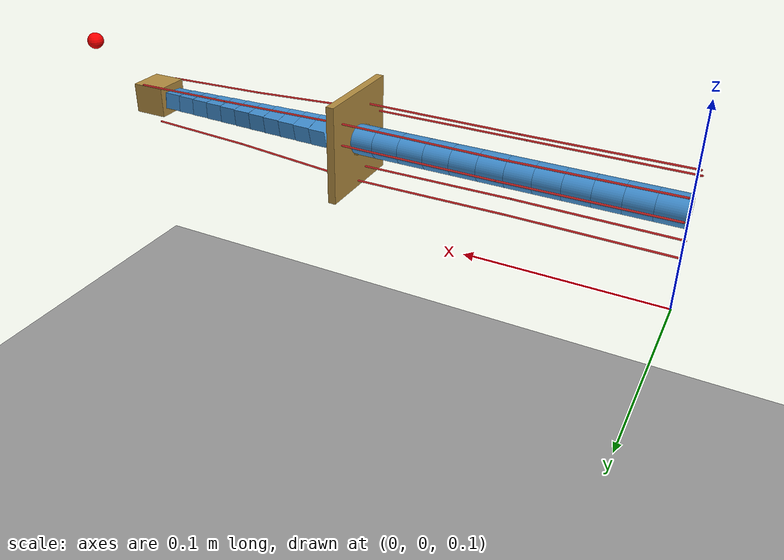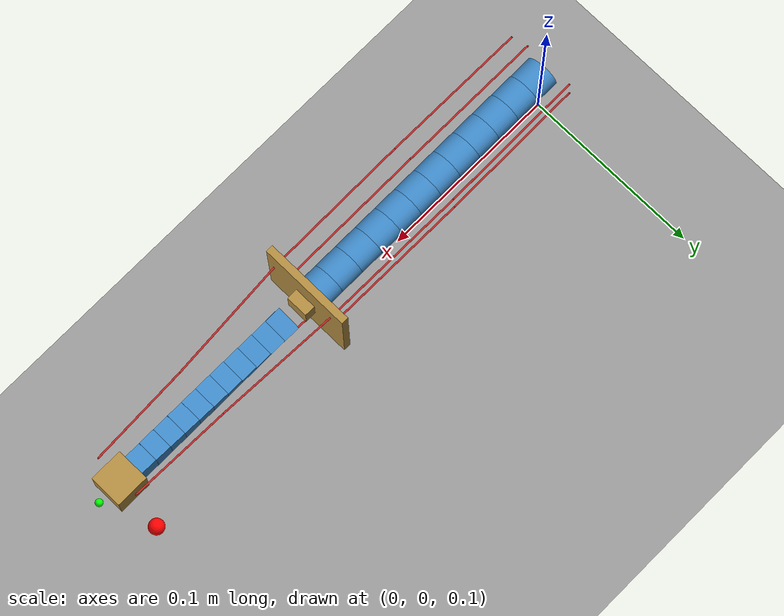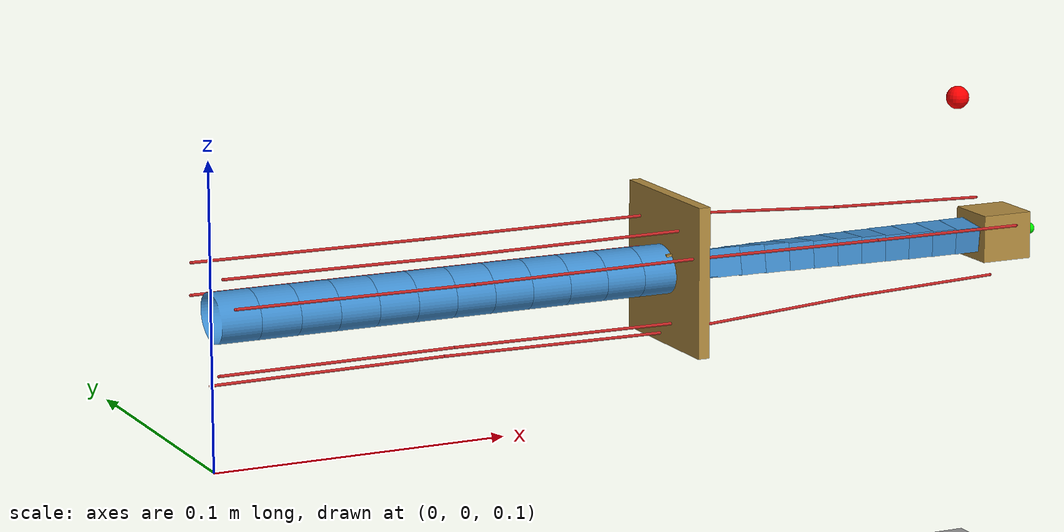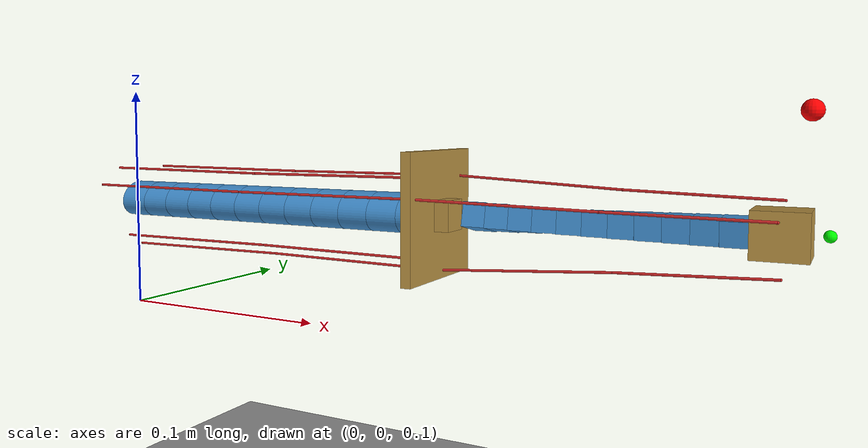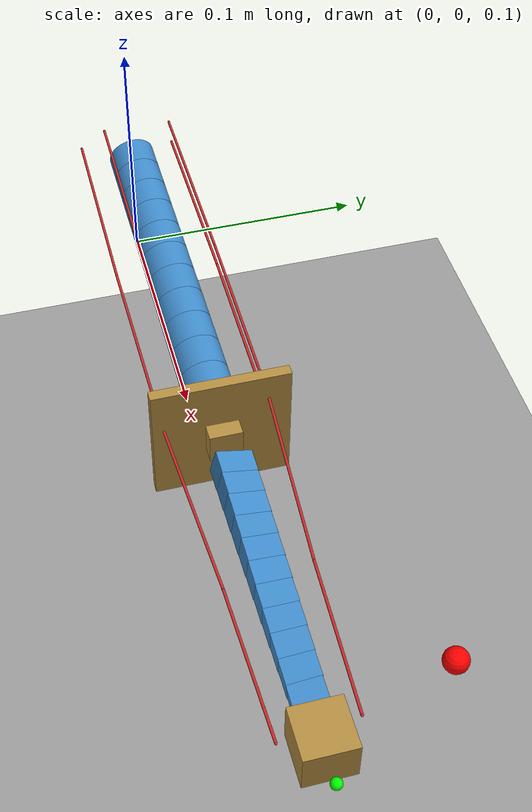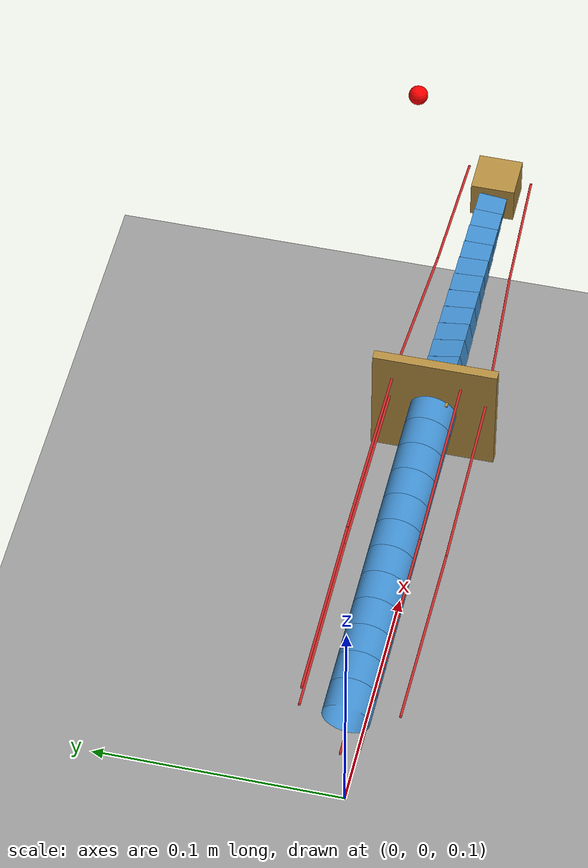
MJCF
<?xml version='1.0' encoding='utf-8'?>
<mujoco model="serial_tendon_family"><compiler angle="radian" autolimits="true" /><option timestep="0.0005" gravity="0 0 -9.8100000000000005" integrator="implicitfast" /><default><joint limited="false" /><geom contype="1" conaffinity="2" friction="0 0 0" /></default><asset><mesh name="near_cell_0_section" vertex="0 -0.0094999999999999998 -2.2789355145497161e-18 0 -0.009418726183051198 -0.0009919990608723945 0 -0.009176295349746148 -0.0019670247427791597 0 -0.0087768555588572227 -0.0029083940859746843 0 -0.0082272413359521651 -0.0038000000000000013 0 -0.0075368567327667333 -0.0046265868604662775 0 -0.0067175144212721994 -0.0053740115370177624 0 -0.005783233575582844 -0.0060294853862133888 0 -0.004749999999999999 -0.006581793068761734 0 -0.0036354926074683514 -0.0070214844470857796 0 -0.0024587809284739473 -0.0073410362797969187 0 -0.0012399988260904896 -0.0075349809464409587 0 1.0438255109511447e-18 -0.0075999999999999991 0 0.00123999882609049 -0.0075349809464409587 0 0.0024587809284739477 -0.0073410362797969187 0 0.0036354926074683518 -0.0070214844470857796 0 0.0047499999999999999 -0.0065817930687617323 0 0.0057832335755828431 -0.006029485386213387 0 0.006717514421272202 -0.0053740115370177598 0 0.0075368567327667333 -0.0046265868604662757 0 0.0082272413359521651 -0.0038000000000000009 0 0.0087768555588572245 -0.0029083940859746808 0 0.0091762953497461497 -0.0019670247427791576 0 0.009418726183051198 -0.00099199906087239255 0 0.009499999999999998 1.4641595657155319e-18 0 0.009418726183051198 0.00099199906087239233 0 0.0091762953497461497 0.0019670247427791563 0 0.0087768555588572262 0.00290839408597468 0 0.0082272413359521668 0.0038 0 0.0075368567327667351 0.0046265868604662757 0 0.0067175144212722037 0.0053740115370177598 0 0.0057832335755828466 0.006029485386213387 0 0.0047500000000000025 0.0065817930687617331 0 0.0036354926074683562 0.0070214844470857778 0 0.0024587809284739525 0.0073410362797969178 0 0.001239998826090497 0.0075349809464409579 0 -3.1272820372996985e-19 0.0076 0 -0.001239998826090489 0.0075349809464409596 0 -0.0024587809284739447 0.0073410362797969187 0 -0.0036354926074683492 0.0070214844470857804 0 -0.0047499999999999955 0.0065817930687617357 0 -0.0057832335755828405 0.0060294853862133905 0 -0.0067175144212722002 0.0053740115370177607 0 -0.0075368567327667325 0.0046265868604662766 0 -0.0082272413359521651 0.0038000000000000013 0 -0.008776855558857221 0.0029083940859746847 0 -0.0091762953497461462 0.0019670247427791619 0 -0.009418726183051198 0.0009919990608723971 0.013333333333333334 -0.0094999999999999998 -2.2789355145497161e-18 0.013333333333333334 -0.009418726183051198 -0.0009919990608723945 0.013333333333333334 -0.009176295349746148 -0.0019670247427791597 0.013333333333333334 -0.0087768555588572227 -0.0029083940859746843 0.013333333333333334 -0.0082272413359521651 -0.0038000000000000013 0.013333333333333334 -0.0075368567327667333 -0.0046265868604662775 0.013333333333333334 -0.0067175144212721994 -0.0053740115370177624 0.013333333333333334 -0.005783233575582844 -0.0060294853862133888 0.013333333333333334 -0.004749999999999999 -0.006581793068761734 0.013333333333333334 -0.0036354926074683514 -0.0070214844470857796 0.013333333333333334 -0.0024587809284739473 -0.0073410362797969187 0.013333333333333334 -0.0012399988260904896 -0.0075349809464409587 0.013333333333333334 1.0438255109511447e-18 -0.0075999999999999991 0.013333333333333334 0.00123999882609049 -0.0075349809464409587 0.013333333333333334 0.0024587809284739477 -0.0073410362797969187 0.013333333333333334 0.0036354926074683518 -0.0070214844470857796 0.013333333333333334 0.0047499999999999999 -0.0065817930687617323 0.013333333333333334 0.0057832335755828431 -0.006029485386213387 0.013333333333333334 0.006717514421272202 -0.0053740115370177598 0.013333333333333334 0.0075368567327667333 -0.0046265868604662757 0.013333333333333334 0.0082272413359521651 -0.0038000000000000009 0.013333333333333334 0.0087768555588572245 -0.0029083940859746808 0.013333333333333334 0.0091762953497461497 -0.0019670247427791576 0.013333333333333334 0.009418726183051198 -0.00099199906087239255 0.013333333333333334 0.009499999999999998 1.4641595657155319e-18 0.013333333333333334 0.009418726183051198 0.00099199906087239233 0.013333333333333334 0.0091762953497461497 0.0019670247427791563 0.013333333333333334 0.0087768555588572262 0.00290839408597468 0.013333333333333334 0.0082272413359521668 0.0038 0.013333333333333334 0.0075368567327667351 0.0046265868604662757 0.013333333333333334 0.0067175144212722037 0.0053740115370177598 0.013333333333333334 0.0057832335755828466 0.006029485386213387 0.013333333333333334 0.0047500000000000025 0.0065817930687617331 0.013333333333333334 0.0036354926074683562 0.0070214844470857778 0.013333333333333334 0.0024587809284739525 0.0073410362797969178 0.013333333333333334 0.001239998826090497 0.0075349809464409579 0.013333333333333334 -3.1272820372996985e-19 0.0076 0.013333333333333334 -0.001239998826090489 0.0075349809464409596 0.013333333333333334 -0.0024587809284739447 0.0073410362797969187 0.013333333333333334 -0.0036354926074683492 0.0070214844470857804 0.013333333333333334 -0.0047499999999999955 0.0065817930687617357 0.013333333333333334 -0.0057832335755828405 0.0060294853862133905 0.013333333333333334 -0.0067175144212722002 0.0053740115370177607 0.013333333333333334 -0.0075368567327667325 0.0046265868604662766 0.013333333333333334 -0.0082272413359521651 0.0038000000000000013 0.013333333333333334 -0.008776855558857221 0.0029083940859746847 0.013333333333333334 -0.0091762953497461462 0.0019670247427791619 0.013333333333333334 -0.009418726183051198 0.0009919990608723971" face="0 1 49 0 49 48 1 2 50 1 50 49 2 3 51 2 51 50 3 4 52 3 52 51 4 5 53 4 53 52 5 6 54 5 54 53 6 7 55 6 55 54 7 8 56 7 56 55 8 9 57 8 57 56 9 10 58 9 58 57 10 11 59 10 59 58 11 12 60 11 60 59 12 13 61 12 61 60 13 14 62 13 62 61 14 15 63 14 63 62 15 16 64 15 64 63 16 17 65 16 65 64 17 18 66 17 66 65 18 19 67 18 67 66 19 20 68 19 68 67 20 21 69 20 69 68 21 22 70 21 70 69 22 23 71 22 71 70 23 24 72 23 72 71 24 25 73 24 73 72 25 26 74 25 74 73 26 27 75 26 75 74 27 28 76 27 76 75 28 29 77 28 77 76 29 30 78 29 78 77 30 31 79 30 79 78 31 32 80 31 80 79 32 33 81 32 81 80 33 34 82 33 82 81 34 35 83 34 83 82 35 36 84 35 84 83 36 37 85 36 85 84 37 38 86 37 86 85 38 39 87 38 87 86 39 40 88 39 88 87 40 41 89 40 89 88 41 42 90 41 90 89 42 43 91 42 91 90 43 44 92 43 92 91 44 45 93 44 93 92 45 46 94 45 94 93 46 47 95 46 95 94 47 0 48 47 48 95" /><mesh name="near_cell_1_section" vertex="0 -0.0094999999999999998 -2.2789355145497161e-18 0 -0.009418726183051198 -0.0009919990608723945 0 -0.009176295349746148 -0.0019670247427791597 0 -0.0087768555588572227 -0.0029083940859746843 0 -0.0082272413359521651 -0.0038000000000000013 0 -0.0075368567327667333 -0.0046265868604662775 0 -0.0067175144212721994 -0.0053740115370177624 0 -0.005783233575582844 -0.0060294853862133888 0 -0.004749999999999999 -0.006581793068761734 0 -0.0036354926074683514 -0.0070214844470857796 0 -0.0024587809284739473 -0.0073410362797969187 0 -0.0012399988260904896 -0.0075349809464409587 0 1.0438255109511447e-18 -0.0075999999999999991 0 0.00123999882609049 -0.0075349809464409587 0 0.0024587809284739477 -0.0073410362797969187 0 0.0036354926074683518 -0.0070214844470857796 0 0.0047499999999999999 -0.0065817930687617323 0 0.0057832335755828431 -0.006029485386213387 0 0.006717514421272202 -0.0053740115370177598 0 0.0075368567327667333 -0.0046265868604662757 0 0.0082272413359521651 -0.0038000000000000009 0 0.0087768555588572245 -0.0029083940859746808 0 0.0091762953497461497 -0.0019670247427791576 0 0.009418726183051198 -0.00099199906087239255 0 0.009499999999999998 1.4641595657155319e-18 0 0.009418726183051198 0.00099199906087239233 0 0.0091762953497461497 0.0019670247427791563 0 0.0087768555588572262 0.00290839408597468 0 0.0082272413359521668 0.0038 0 0.0075368567327667351 0.0046265868604662757 0 0.0067175144212722037 0.0053740115370177598 0 0.0057832335755828466 0.006029485386213387 0 0.0047500000000000025 0.0065817930687617331 0 0.0036354926074683562 0.0070214844470857778 0 0.0024587809284739525 0.0073410362797969178 0 0.001239998826090497 0.0075349809464409579 0 -3.1272820372996985e-19 0.0076 0 -0.001239998826090489 0.0075349809464409596 0 -0.0024587809284739447 0.0073410362797969187 0 -0.0036354926074683492 0.0070214844470857804 0 -0.0047499999999999955 0.0065817930687617357 0 -0.0057832335755828405 0.0060294853862133905 0 -0.0067175144212722002 0.0053740115370177607 0 -0.0075368567327667325 0.0046265868604662766 0 -0.0082272413359521651 0.0038000000000000013 0 -0.008776855558857221 0.0029083940859746847 0 -0.0091762953497461462 0.0019670247427791619 0 -0.009418726183051198 0.0009919990608723971 0.013333333333333334 -0.0094999999999999998 -2.2789355145497161e-18 0.013333333333333334 -0.009418726183051198 -0.0009919990608723945 0.013333333333333334 -0.009176295349746148 -0.0019670247427791597 0.013333333333333334 -0.0087768555588572227 -0.0029083940859746843 0.013333333333333334 -0.0082272413359521651 -0.0038000000000000013 0.013333333333333334 -0.0075368567327667333 -0.0046265868604662775 0.013333333333333334 -0.0067175144212721994 -0.0053740115370177624 0.013333333333333334 -0.005783233575582844 -0.0060294853862133888 0.013333333333333334 -0.004749999999999999 -0.006581793068761734 0.013333333333333334 -0.0036354926074683514 -0.0070214844470857796 0.013333333333333334 -0.0024587809284739473 -0.0073410362797969187 0.013333333333333334 -0.0012399988260904896 -0.0075349809464409587 0.013333333333333334 1.0438255109511447e-18 -0.0075999999999999991 0.013333333333333334 0.00123999882609049 -0.0075349809464409587 0.013333333333333334 0.0024587809284739477 -0.0073410362797969187 0.013333333333333334 0.0036354926074683518 -0.0070214844470857796 0.013333333333333334 0.0047499999999999999 -0.0065817930687617323 0.013333333333333334 0.0057832335755828431 -0.006029485386213387 0.013333333333333334 0.006717514421272202 -0.0053740115370177598 0.013333333333333334 0.0075368567327667333 -0.0046265868604662757 0.013333333333333334 0.0082272413359521651 -0.0038000000000000009 0.013333333333333334 0.0087768555588572245 -0.0029083940859746808 0.013333333333333334 0.0091762953497461497 -0.0019670247427791576 0.013333333333333334 0.009418726183051198 -0.00099199906087239255 0.013333333333333334 0.009499999999999998 1.4641595657155319e-18 0.013333333333333334 0.009418726183051198 0.00099199906087239233 0.013333333333333334 0.0091762953497461497 0.0019670247427791563 0.013333333333333334 0.0087768555588572262 0.00290839408597468 0.013333333333333334 0.0082272413359521668 0.0038 0.013333333333333334 0.0075368567327667351 0.0046265868604662757 0.013333333333333334 0.0067175144212722037 0.0053740115370177598 0.013333333333333334 0.0057832335755828466 0.006029485386213387 0.013333333333333334 0.0047500000000000025 0.0065817930687617331 0.013333333333333334 0.0036354926074683562 0.0070214844470857778 0.013333333333333334 0.0024587809284739525 0.0073410362797969178 0.013333333333333334 0.001239998826090497 0.0075349809464409579 0.013333333333333334 -3.1272820372996985e-19 0.0076 0.013333333333333334 -0.001239998826090489 0.0075349809464409596 0.013333333333333334 -0.0024587809284739447 0.0073410362797969187 0.013333333333333334 -0.0036354926074683492 0.0070214844470857804 0.013333333333333334 -0.0047499999999999955 0.0065817930687617357 0.013333333333333334 -0.0057832335755828405 0.0060294853862133905 0.013333333333333334 -0.0067175144212722002 0.0053740115370177607 0.013333333333333334 -0.0075368567327667325 0.0046265868604662766 0.013333333333333334 -0.0082272413359521651 0.0038000000000000013 0.013333333333333334 -0.008776855558857221 0.0029083940859746847 0.013333333333333334 -0.0091762953497461462 0.0019670247427791619 0.013333333333333334 -0.009418726183051198 0.0009919990608723971" face="0 1 49 0 49 48 1 2 50 1 50 49 2 3 51 2 51 50 3 4 52 3 52 51 4 5 53 4 53 52 5 6 54 5 54 53 6 7 55 6 55 54 7 8 56 7 56 55 8 9 57 8 57 56 9 10 58 9 58 57 10 11 59 10 59 58 11 12 60 11 60 59 12 13 61 12 61 60 13 14 62 13 62 61 14 15 63 14 63 62 15 16 64 15 64 63 16 17 65 16 65 64 17 18 66 17 66 65 18 19 67 18 67 66 19 20 68 19 68 67 20 21 69 20 69 68 21 22 70 21 70 69 22 23 71 22 71 70 23 24 72 23 72 71 24 25 73 24 73 72 25 26 74 25 74 73 26 27 75 26 75 74 27 28 76 27 76 75 28 29 77 28 77 76 29 30 78 29 78 77 30 31 79 30 79 78 31 32 80 31 80 79 32 33 81 32 81 80 33 34 82 33 82 81 34 35 83 34 83 82 35 36 84 35 84 83 36 37 85 36 85 84 37 38 86 37 86 85 38 39 87 38 87 86 39 40 88 39 88 87 40 41 89 40 89 88 41 42 90 41 90 89 42 43 91 42 91 90 43 44 92 43 92 91 44 45 93 44 93 92 45 46 94 45 94 93 46 47 95 46 95 94 47 0 48 47 48 95" /><mesh name="near_cell_2_section" vertex="0 -0.0094999999999999998 -2.2789355145497161e-18 0 -0.009418726183051198 -0.0009919990608723945 0 -0.009176295349746148 -0.0019670247427791597 0 -0.0087768555588572227 -0.0029083940859746843 0 -0.0082272413359521651 -0.0038000000000000013 0 -0.0075368567327667333 -0.0046265868604662775 0 -0.0067175144212721994 -0.0053740115370177624 0 -0.005783233575582844 -0.0060294853862133888 0 -0.004749999999999999 -0.006581793068761734 0 -0.0036354926074683514 -0.0070214844470857796 0 -0.0024587809284739473 -0.0073410362797969187 0 -0.0012399988260904896 -0.0075349809464409587 0 1.0438255109511447e-18 -0.0075999999999999991 0 0.00123999882609049 -0.0075349809464409587 0 0.0024587809284739477 -0.0073410362797969187 0 0.0036354926074683518 -0.0070214844470857796 0 0.0047499999999999999 -0.0065817930687617323 0 0.0057832335755828431 -0.006029485386213387 0 0.006717514421272202 -0.0053740115370177598 0 0.0075368567327667333 -0.0046265868604662757 0 0.0082272413359521651 -0.0038000000000000009 0 0.0087768555588572245 -0.0029083940859746808 0 0.0091762953497461497 -0.0019670247427791576 0 0.009418726183051198 -0.00099199906087239255 0 0.009499999999999998 1.4641595657155319e-18 0 0.009418726183051198 0.00099199906087239233 0 0.0091762953497461497 0.0019670247427791563 0 0.0087768555588572262 0.00290839408597468 0 0.0082272413359521668 0.0038 0 0.0075368567327667351 0.0046265868604662757 0 0.0067175144212722037 0.0053740115370177598 0 0.0057832335755828466 0.006029485386213387 0 0.0047500000000000025 0.0065817930687617331 0 0.0036354926074683562 0.0070214844470857778 0 0.0024587809284739525 0.0073410362797969178 0 0.001239998826090497 0.0075349809464409579 0 -3.1272820372996985e-19 0.0076 0 -0.001239998826090489 0.0075349809464409596 0 -0.0024587809284739447 0.0073410362797969187 0 -0.0036354926074683492 0.0070214844470857804 0 -0.0047499999999999955 0.0065817930687617357 0 -0.0057832335755828405 0.0060294853862133905 0 -0.0067175144212722002 0.0053740115370177607 0 -0.0075368567327667325 0.0046265868604662766 0 -0.0082272413359521651 0.0038000000000000013 0 -0.008776855558857221 0.0029083940859746847 0 -0.0091762953497461462 0.0019670247427791619 0 -0.009418726183051198 0.0009919990608723971 0.013333333333333334 -0.0094999999999999998 -2.2789355145497161e-18 0.013333333333333334 -0.009418726183051198 -0.0009919990608723945 0.013333333333333334 -0.009176295349746148 -0.0019670247427791597 0.013333333333333334 -0.0087768555588572227 -0.0029083940859746843 0.013333333333333334 -0.0082272413359521651 -0.0038000000000000013 0.013333333333333334 -0.0075368567327667333 -0.0046265868604662775 0.013333333333333334 -0.0067175144212721994 -0.0053740115370177624 0.013333333333333334 -0.005783233575582844 -0.0060294853862133888 0.013333333333333334 -0.004749999999999999 -0.006581793068761734 0.013333333333333334 -0.0036354926074683514 -0.0070214844470857796 0.013333333333333334 -0.0024587809284739473 -0.0073410362797969187 0.013333333333333334 -0.0012399988260904896 -0.0075349809464409587 0.013333333333333334 1.0438255109511447e-18 -0.0075999999999999991 0.013333333333333334 0.00123999882609049 -0.0075349809464409587 0.013333333333333334 0.0024587809284739477 -0.0073410362797969187 0.013333333333333334 0.0036354926074683518 -0.0070214844470857796 0.013333333333333334 0.0047499999999999999 -0.0065817930687617323 0.013333333333333334 0.0057832335755828431 -0.006029485386213387 0.013333333333333334 0.006717514421272202 -0.0053740115370177598 0.013333333333333334 0.0075368567327667333 -0.0046265868604662757 0.013333333333333334 0.0082272413359521651 -0.0038000000000000009 0.013333333333333334 0.0087768555588572245 -0.0029083940859746808 0.013333333333333334 0.0091762953497461497 -0.0019670247427791576 0.013333333333333334 0.009418726183051198 -0.00099199906087239255 0.013333333333333334 0.009499999999999998 1.4641595657155319e-18 0.013333333333333334 0.009418726183051198 0.00099199906087239233 0.013333333333333334 0.0091762953497461497 0.0019670247427791563 0.013333333333333334 0.0087768555588572262 0.00290839408597468 0.013333333333333334 0.0082272413359521668 0.0038 0.013333333333333334 0.0075368567327667351 0.0046265868604662757 0.013333333333333334 0.0067175144212722037 0.0053740115370177598 0.013333333333333334 0.0057832335755828466 0.006029485386213387 0.013333333333333334 0.0047500000000000025 0.0065817930687617331 0.013333333333333334 0.0036354926074683562 0.0070214844470857778 0.013333333333333334 0.0024587809284739525 0.0073410362797969178 0.013333333333333334 0.001239998826090497 0.0075349809464409579 0.013333333333333334 -3.1272820372996985e-19 0.0076 0.013333333333333334 -0.001239998826090489 0.0075349809464409596 0.013333333333333334 -0.0024587809284739447 0.0073410362797969187 0.013333333333333334 -0.0036354926074683492 0.0070214844470857804 0.013333333333333334 -0.0047499999999999955 0.0065817930687617357 0.013333333333333334 -0.0057832335755828405 0.0060294853862133905 0.013333333333333334 -0.0067175144212722002 0.0053740115370177607 0.013333333333333334 -0.0075368567327667325 0.0046265868604662766 0.013333333333333334 -0.0082272413359521651 0.0038000000000000013 0.013333333333333334 -0.008776855558857221 0.0029083940859746847 0.013333333333333334 -0.0091762953497461462 0.0019670247427791619 0.013333333333333334 -0.009418726183051198 0.0009919990608723971" face="0 1 49 0 49 48 1 2 50 1 50 49 2 3 51 2 51 50 3 4 52 3 52 51 4 5 53 4 53 52 5 6 54 5 54 53 6 7 55 6 55 54 7 8 56 7 56 55 8 9 57 8 57 56 9 10 58 9 58 57 10 11 59 10 59 58 11 12 60 11 60 59 12 13 61 12 61 60 13 14 62 13 62 61 14 15 63 14 63 62 15 16 64 15 64 63 16 17 65 16 65 64 17 18 66 17 66 65 18 19 67 18 67 66 19 20 68 19 68 67 20 21 69 20 69 68 21 22 70 21 70 69 22 23 71 22 71 70 23 24 72 23 72 71 24 25 73 24 73 72 25 26 74 25 74 73 26 27 75 26 75 74 27 28 76 27 76 75 28 29 77 28 77 76 29 30 78 29 78 77 30 31 79 30 79 78 31 32 80 31 80 79 32 33 81 32 81 80 33 34 82 33 82 81 34 35 83 34 83 82 35 36 84 35 84 83 36 37 85 36 85 84 37 38 86 37 86 85 38 39 87 38 87 86 39 40 88 39 88 87 40 41 89 40 89 88 41 42 90 41 90 89 42 43 91 42 91 90 43 44 92 43 92 91 44 45 93 44 93 92 45 46 94 45 94 93 46 47 95 46 95 94 47 0 48 47 48 95" /><mesh name="near_cell_3_section" vertex="0 -0.0094999999999999998 -2.2789355145497161e-18 0 -0.009418726183051198 -0.0009919990608723945 0 -0.009176295349746148 -0.0019670247427791597 0 -0.0087768555588572227 -0.0029083940859746843 0 -0.0082272413359521651 -0.0038000000000000013 0 -0.0075368567327667333 -0.0046265868604662775 0 -0.0067175144212721994 -0.0053740115370177624 0 -0.005783233575582844 -0.0060294853862133888 0 -0.004749999999999999 -0.006581793068761734 0 -0.0036354926074683514 -0.0070214844470857796 0 -0.0024587809284739473 -0.0073410362797969187 0 -0.0012399988260904896 -0.0075349809464409587 0 1.0438255109511447e-18 -0.0075999999999999991 0 0.00123999882609049 -0.0075349809464409587 0 0.0024587809284739477 -0.0073410362797969187 0 0.0036354926074683518 -0.0070214844470857796 0 0.0047499999999999999 -0.0065817930687617323 0 0.0057832335755828431 -0.006029485386213387 0 0.006717514421272202 -0.0053740115370177598 0 0.0075368567327667333 -0.0046265868604662757 0 0.0082272413359521651 -0.0038000000000000009 0 0.0087768555588572245 -0.0029083940859746808 0 0.0091762953497461497 -0.0019670247427791576 0 0.009418726183051198 -0.00099199906087239255 0 0.009499999999999998 1.4641595657155319e-18 0 0.009418726183051198 0.00099199906087239233 0 0.0091762953497461497 0.0019670247427791563 0 0.0087768555588572262 0.00290839408597468 0 0.0082272413359521668 0.0038 0 0.0075368567327667351 0.0046265868604662757 0 0.0067175144212722037 0.0053740115370177598 0 0.0057832335755828466 0.006029485386213387 0 0.0047500000000000025 0.0065817930687617331 0 0.0036354926074683562 0.0070214844470857778 0 0.0024587809284739525 0.0073410362797969178 0 0.001239998826090497 0.0075349809464409579 0 -3.1272820372996985e-19 0.0076 0 -0.001239998826090489 0.0075349809464409596 0 -0.0024587809284739447 0.0073410362797969187 0 -0.0036354926074683492 0.0070214844470857804 0 -0.0047499999999999955 0.0065817930687617357 0 -0.0057832335755828405 0.0060294853862133905 0 -0.0067175144212722002 0.0053740115370177607 0 -0.0075368567327667325 0.0046265868604662766 0 -0.0082272413359521651 0.0038000000000000013 0 -0.008776855558857221 0.0029083940859746847 0 -0.0091762953497461462 0.0019670247427791619 0 -0.009418726183051198 0.0009919990608723971 0.013333333333333334 -0.0094999999999999998 -2.2789355145497161e-18 0.013333333333333334 -0.009418726183051198 -0.0009919990608723945 0.013333333333333334 -0.009176295349746148 -0.0019670247427791597 0.013333333333333334 -0.0087768555588572227 -0.0029083940859746843 0.013333333333333334 -0.0082272413359521651 -0.0038000000000000013 0.013333333333333334 -0.0075368567327667333 -0.0046265868604662775 0.013333333333333334 -0.0067175144212721994 -0.0053740115370177624 0.013333333333333334 -0.005783233575582844 -0.0060294853862133888 0.013333333333333334 -0.004749999999999999 -0.006581793068761734 0.013333333333333334 -0.0036354926074683514 -0.0070214844470857796 0.013333333333333334 -0.0024587809284739473 -0.0073410362797969187 0.013333333333333334 -0.0012399988260904896 -0.0075349809464409587 0.013333333333333334 1.0438255109511447e-18 -0.0075999999999999991 0.013333333333333334 0.00123999882609049 -0.0075349809464409587 0.013333333333333334 0.0024587809284739477 -0.0073410362797969187 0.013333333333333334 0.0036354926074683518 -0.0070214844470857796 0.013333333333333334 0.0047499999999999999 -0.0065817930687617323 0.013333333333333334 0.0057832335755828431 -0.006029485386213387 0.013333333333333334 0.006717514421272202 -0.0053740115370177598 0.013333333333333334 0.0075368567327667333 -0.0046265868604662757 0.013333333333333334 0.0082272413359521651 -0.0038000000000000009 0.013333333333333334 0.0087768555588572245 -0.0029083940859746808 0.013333333333333334 0.0091762953497461497 -0.0019670247427791576 0.013333333333333334 0.009418726183051198 -0.00099199906087239255 0.013333333333333334 0.009499999999999998 1.4641595657155319e-18 0.013333333333333334 0.009418726183051198 0.00099199906087239233 0.013333333333333334 0.0091762953497461497 0.0019670247427791563 0.013333333333333334 0.0087768555588572262 0.00290839408597468 0.013333333333333334 0.0082272413359521668 0.0038 0.013333333333333334 0.0075368567327667351 0.0046265868604662757 0.013333333333333334 0.0067175144212722037 0.0053740115370177598 0.013333333333333334 0.0057832335755828466 0.006029485386213387 0.013333333333333334 0.0047500000000000025 0.0065817930687617331 0.013333333333333334 0.0036354926074683562 0.0070214844470857778 0.013333333333333334 0.0024587809284739525 0.0073410362797969178 0.013333333333333334 0.001239998826090497 0.0075349809464409579 0.013333333333333334 -3.1272820372996985e-19 0.0076 0.013333333333333334 -0.001239998826090489 0.0075349809464409596 0.013333333333333334 -0.0024587809284739447 0.0073410362797969187 0.013333333333333334 -0.0036354926074683492 0.0070214844470857804 0.013333333333333334 -0.0047499999999999955 0.0065817930687617357 0.013333333333333334 -0.0057832335755828405 0.0060294853862133905 0.013333333333333334 -0.0067175144212722002 0.0053740115370177607 0.013333333333333334 -0.0075368567327667325 0.0046265868604662766 0.013333333333333334 -0.0082272413359521651 0.0038000000000000013 0.013333333333333334 -0.008776855558857221 0.0029083940859746847 0.013333333333333334 -0.0091762953497461462 0.0019670247427791619 0.013333333333333334 -0.009418726183051198 0.0009919990608723971" face="0 1 49 0 49 48 1 2 50 1 50 49 2 3 51 2 51 50 3 4 52 3 52 51 4 5 53 4 53 52 5 6 54 5 54 53 6 7 55 6 55 54 7 8 56 7 56 55 8 9 57 8 57 56 9 10 58 9 58 57 10 11 59 10 59 58 11 12 60 11 60 59 12 13 61 12 61 60 13 14 62 13 62 61 14 15 63 14 63 62 15 16 64 15 64 63 16 17 65 16 65 64 17 18 66 17 66 65 18 19 67 18 67 66 19 20 68 19 68 67 20 21 69 20 69 68 21 22 70 21 70 69 22 23 71 22 71 70 23 24 72 23 72 71 24 25 73 24 73 72 25 26 74 25 74 73 26 27 75 26 75 74 27 28 76 27 76 75 28 29 77 28 77 76 29 30 78 29 78 77 30 31 79 30 79 78 31 32 80 31 80 79 32 33 81 32 81 80 33 34 82 33 82 81 34 35 83 34 83 82 35 36 84 35 84 83 36 37 85 36 85 84 37 38 86 37 86 85 38 39 87 38 87 86 39 40 88 39 88 87 40 41 89 40 89 88 41 42 90 41 90 89 42 43 91 42 91 90 43 44 92 43 92 91 44 45 93 44 93 92 45 46 94 45 94 93 46 47 95 46 95 94 47 0 48 47 48 95" /><mesh name="near_cell_4_section" vertex="0 -0.0094999999999999998 -2.2789355145497161e-18 0 -0.009418726183051198 -0.0009919990608723945 0 -0.009176295349746148 -0.0019670247427791597 0 -0.0087768555588572227 -0.0029083940859746843 0 -0.0082272413359521651 -0.0038000000000000013 0 -0.0075368567327667333 -0.0046265868604662775 0 -0.0067175144212721994 -0.0053740115370177624 0 -0.005783233575582844 -0.0060294853862133888 0 -0.004749999999999999 -0.006581793068761734 0 -0.0036354926074683514 -0.0070214844470857796 0 -0.0024587809284739473 -0.0073410362797969187 0 -0.0012399988260904896 -0.0075349809464409587 0 1.0438255109511447e-18 -0.0075999999999999991 0 0.00123999882609049 -0.0075349809464409587 0 0.0024587809284739477 -0.0073410362797969187 0 0.0036354926074683518 -0.0070214844470857796 0 0.0047499999999999999 -0.0065817930687617323 0 0.0057832335755828431 -0.006029485386213387 0 0.006717514421272202 -0.0053740115370177598 0 0.0075368567327667333 -0.0046265868604662757 0 0.0082272413359521651 -0.0038000000000000009 0 0.0087768555588572245 -0.0029083940859746808 0 0.0091762953497461497 -0.0019670247427791576 0 0.009418726183051198 -0.00099199906087239255 0 0.009499999999999998 1.4641595657155319e-18 0 0.009418726183051198 0.00099199906087239233 0 0.0091762953497461497 0.0019670247427791563 0 0.0087768555588572262 0.00290839408597468 0 0.0082272413359521668 0.0038 0 0.0075368567327667351 0.0046265868604662757 0 0.0067175144212722037 0.0053740115370177598 0 0.0057832335755828466 0.006029485386213387 0 0.0047500000000000025 0.0065817930687617331 0 0.0036354926074683562 0.0070214844470857778 0 0.0024587809284739525 0.0073410362797969178 0 0.001239998826090497 0.0075349809464409579 0 -3.1272820372996985e-19 0.0076 0 -0.001239998826090489 0.0075349809464409596 0 -0.0024587809284739447 0.0073410362797969187 0 -0.0036354926074683492 0.0070214844470857804 0 -0.0047499999999999955 0.0065817930687617357 0 -0.0057832335755828405 0.0060294853862133905 0 -0.0067175144212722002 0.0053740115370177607 0 -0.0075368567327667325 0.0046265868604662766 0 -0.0082272413359521651 0.0038000000000000013 0 -0.008776855558857221 0.0029083940859746847 0 -0.0091762953497461462 0.0019670247427791619 0 -0.009418726183051198 0.0009919990608723971 0.013333333333333334 -0.0094999999999999998 -2.2789355145497161e-18 0.013333333333333334 -0.009418726183051198 -0.0009919990608723945 0.013333333333333334 -0.009176295349746148 -0.0019670247427791597 0.013333333333333334 -0.0087768555588572227 -0.0029083940859746843 0.013333333333333334 -0.0082272413359521651 -0.0038000000000000013 0.013333333333333334 -0.0075368567327667333 -0.0046265868604662775 0.013333333333333334 -0.0067175144212721994 -0.0053740115370177624 0.013333333333333334 -0.005783233575582844 -0.0060294853862133888 0.013333333333333334 -0.004749999999999999 -0.006581793068761734 0.013333333333333334 -0.0036354926074683514 -0.0070214844470857796 0.013333333333333334 -0.0024587809284739473 -0.0073410362797969187 0.013333333333333334 -0.0012399988260904896 -0.0075349809464409587 0.013333333333333334 1.0438255109511447e-18 -0.0075999999999999991 0.013333333333333334 0.00123999882609049 -0.0075349809464409587 0.013333333333333334 0.0024587809284739477 -0.0073410362797969187 0.013333333333333334 0.0036354926074683518 -0.0070214844470857796 0.013333333333333334 0.0047499999999999999 -0.0065817930687617323 0.013333333333333334 0.0057832335755828431 -0.006029485386213387 0.013333333333333334 0.006717514421272202 -0.0053740115370177598 0.013333333333333334 0.0075368567327667333 -0.0046265868604662757 0.013333333333333334 0.0082272413359521651 -0.0038000000000000009 0.013333333333333334 0.0087768555588572245 -0.0029083940859746808 0.013333333333333334 0.0091762953497461497 -0.0019670247427791576 0.013333333333333334 0.009418726183051198 -0.00099199906087239255 0.013333333333333334 0.009499999999999998 1.4641595657155319e-18 0.013333333333333334 0.009418726183051198 0.00099199906087239233 0.013333333333333334 0.0091762953497461497 0.0019670247427791563 0.013333333333333334 0.0087768555588572262 0.00290839408597468 0.013333333333333334 0.0082272413359521668 0.0038 0.013333333333333334 0.0075368567327667351 0.0046265868604662757 0.013333333333333334 0.0067175144212722037 0.0053740115370177598 0.013333333333333334 0.0057832335755828466 0.006029485386213387 0.013333333333333334 0.0047500000000000025 0.0065817930687617331 0.013333333333333334 0.0036354926074683562 0.0070214844470857778 0.013333333333333334 0.0024587809284739525 0.0073410362797969178 0.013333333333333334 0.001239998826090497 0.0075349809464409579 0.013333333333333334 -3.1272820372996985e-19 0.0076 0.013333333333333334 -0.001239998826090489 0.0075349809464409596 0.013333333333333334 -0.0024587809284739447 0.0073410362797969187 0.013333333333333334 -0.0036354926074683492 0.0070214844470857804 0.013333333333333334 -0.0047499999999999955 0.0065817930687617357 0.013333333333333334 -0.0057832335755828405 0.0060294853862133905 0.013333333333333334 -0.0067175144212722002 0.0053740115370177607 0.013333333333333334 -0.0075368567327667325 0.0046265868604662766 0.013333333333333334 -0.0082272413359521651 0.0038000000000000013 0.013333333333333334 -0.008776855558857221 0.0029083940859746847 0.013333333333333334 -0.0091762953497461462 0.0019670247427791619 0.013333333333333334 -0.009418726183051198 0.0009919990608723971" face="0 1 49 0 49 48 1 2 50 1 50 49 2 3 51 2 51 50 3 4 52 3 52 51 4 5 53 4 53 52 5 6 54 5 54 53 6 7 55 6 55 54 7 8 56 7 56 55 8 9 57 8 57 56 9 10 58 9 58 57 10 11 59 10 59 58 11 12 60 11 60 59 12 13 61 12 61 60 13 14 62 13 62 61 14 15 63 14 63 62 15 16 64 15 64 63 16 17 65 16 65 64 17 18 66 17 66 65 18 19 67 18 67 66 19 20 68 19 68 67 20 21 69 20 69 68 21 22 70 21 70 69 22 23 71 22 71 70 23 24 72 23 72 71 24 25 73 24 73 72 25 26 74 25 74 73 26 27 75 26 75 74 27 28 76 27 76 75 28 29 77 28 77 76 29 30 78 29 78 77 30 31 79 30 79 78 31 32 80 31 80 79 32 33 81 32 81 80 33 34 82 33 82 81 34 35 83 34 83 82 35 36 84 35 84 83 36 37 85 36 85 84 37 38 86 37 86 85 38 39 87 38 87 86 39 40 88 39 88 87 40 41 89 40 89 88 41 42 90 41 90 89 42 43 91 42 91 90 43 44 92 43 92 91 44 45 93 44 93 92 45 46 94 45 94 93 46 47 95 46 95 94 47 0 48 47 48 95" /><mesh name="near_cell_5_section" vertex="0 -0.0094999999999999998 -2.2789355145497161e-18 0 -0.009418726183051198 -0.0009919990608723945 0 -0.009176295349746148 -0.0019670247427791597 0 -0.0087768555588572227 -0.0029083940859746843 0 -0.0082272413359521651 -0.0038000000000000013 0 -0.0075368567327667333 -0.0046265868604662775 0 -0.0067175144212721994 -0.0053740115370177624 0 -0.005783233575582844 -0.0060294853862133888 0 -0.004749999999999999 -0.006581793068761734 0 -0.0036354926074683514 -0.0070214844470857796 0 -0.0024587809284739473 -0.0073410362797969187 0 -0.0012399988260904896 -0.0075349809464409587 0 1.0438255109511447e-18 -0.0075999999999999991 0 0.00123999882609049 -0.0075349809464409587 0 0.0024587809284739477 -0.0073410362797969187 0 0.0036354926074683518 -0.0070214844470857796 0 0.0047499999999999999 -0.0065817930687617323 0 0.0057832335755828431 -0.006029485386213387 0 0.006717514421272202 -0.0053740115370177598 0 0.0075368567327667333 -0.0046265868604662757 0 0.0082272413359521651 -0.0038000000000000009 0 0.0087768555588572245 -0.0029083940859746808 0 0.0091762953497461497 -0.0019670247427791576 0 0.009418726183051198 -0.00099199906087239255 0 0.009499999999999998 1.4641595657155319e-18 0 0.009418726183051198 0.00099199906087239233 0 0.0091762953497461497 0.0019670247427791563 0 0.0087768555588572262 0.00290839408597468 0 0.0082272413359521668 0.0038 0 0.0075368567327667351 0.0046265868604662757 0 0.0067175144212722037 0.0053740115370177598 0 0.0057832335755828466 0.006029485386213387 0 0.0047500000000000025 0.0065817930687617331 0 0.0036354926074683562 0.0070214844470857778 0 0.0024587809284739525 0.0073410362797969178 0 0.001239998826090497 0.0075349809464409579 0 -3.1272820372996985e-19 0.0076 0 -0.001239998826090489 0.0075349809464409596 0 -0.0024587809284739447 0.0073410362797969187 0 -0.0036354926074683492 0.0070214844470857804 0 -0.0047499999999999955 0.0065817930687617357 0 -0.0057832335755828405 0.0060294853862133905 0 -0.0067175144212722002 0.0053740115370177607 0 -0.0075368567327667325 0.0046265868604662766 0 -0.0082272413359521651 0.0038000000000000013 0 -0.008776855558857221 0.0029083940859746847 0 -0.0091762953497461462 0.0019670247427791619 0 -0.009418726183051198 0.0009919990608723971 0.013333333333333334 -0.0094999999999999998 -2.2789355145497161e-18 0.013333333333333334 -0.009418726183051198 -0.0009919990608723945 0.013333333333333334 -0.009176295349746148 -0.0019670247427791597 0.013333333333333334 -0.0087768555588572227 -0.0029083940859746843 0.013333333333333334 -0.0082272413359521651 -0.0038000000000000013 0.013333333333333334 -0.0075368567327667333 -0.0046265868604662775 0.013333333333333334 -0.0067175144212721994 -0.0053740115370177624 0.013333333333333334 -0.005783233575582844 -0.0060294853862133888 0.013333333333333334 -0.004749999999999999 -0.006581793068761734 0.013333333333333334 -0.0036354926074683514 -0.0070214844470857796 0.013333333333333334 -0.0024587809284739473 -0.0073410362797969187 0.013333333333333334 -0.0012399988260904896 -0.0075349809464409587 0.013333333333333334 1.0438255109511447e-18 -0.0075999999999999991 0.013333333333333334 0.00123999882609049 -0.0075349809464409587 0.013333333333333334 0.0024587809284739477 -0.0073410362797969187 0.013333333333333334 0.0036354926074683518 -0.0070214844470857796 0.013333333333333334 0.0047499999999999999 -0.0065817930687617323 0.013333333333333334 0.0057832335755828431 -0.006029485386213387 0.013333333333333334 0.006717514421272202 -0.0053740115370177598 0.013333333333333334 0.0075368567327667333 -0.0046265868604662757 0.013333333333333334 0.0082272413359521651 -0.0038000000000000009 0.013333333333333334 0.0087768555588572245 -0.0029083940859746808 0.013333333333333334 0.0091762953497461497 -0.0019670247427791576 0.013333333333333334 0.009418726183051198 -0.00099199906087239255 0.013333333333333334 0.009499999999999998 1.4641595657155319e-18 0.013333333333333334 0.009418726183051198 0.00099199906087239233 0.013333333333333334 0.0091762953497461497 0.0019670247427791563 0.013333333333333334 0.0087768555588572262 0.00290839408597468 0.013333333333333334 0.0082272413359521668 0.0038 0.013333333333333334 0.0075368567327667351 0.0046265868604662757 0.013333333333333334 0.0067175144212722037 0.0053740115370177598 0.013333333333333334 0.0057832335755828466 0.006029485386213387 0.013333333333333334 0.0047500000000000025 0.0065817930687617331 0.013333333333333334 0.0036354926074683562 0.0070214844470857778 0.013333333333333334 0.0024587809284739525 0.0073410362797969178 0.013333333333333334 0.001239998826090497 0.0075349809464409579 0.013333333333333334 -3.1272820372996985e-19 0.0076 0.013333333333333334 -0.001239998826090489 0.0075349809464409596 0.013333333333333334 -0.0024587809284739447 0.0073410362797969187 0.013333333333333334 -0.0036354926074683492 0.0070214844470857804 0.013333333333333334 -0.0047499999999999955 0.0065817930687617357 0.013333333333333334 -0.0057832335755828405 0.0060294853862133905 0.013333333333333334 -0.0067175144212722002 0.0053740115370177607 0.013333333333333334 -0.0075368567327667325 0.0046265868604662766 0.013333333333333334 -0.0082272413359521651 0.0038000000000000013 0.013333333333333334 -0.008776855558857221 0.0029083940859746847 0.013333333333333334 -0.0091762953497461462 0.0019670247427791619 0.013333333333333334 -0.009418726183051198 0.0009919990608723971" face="0 1 49 0 49 48 1 2 50 1 50 49 2 3 51 2 51 50 3 4 52 3 52 51 4 5 53 4 53 52 5 6 54 5 54 53 6 7 55 6 55 54 7 8 56 7 56 55 8 9 57 8 57 56 9 10 58 9 58 57 10 11 59 10 59 58 11 12 60 11 60 59 12 13 61 12 61 60 13 14 62 13 62 61 14 15 63 14 63 62 15 16 64 15 64 63 16 17 65 16 65 64 17 18 66 17 66 65 18 19 67 18 67 66 19 20 68 19 68 67 20 21 69 20 69 68 21 22 70 21 70 69 22 23 71 22 71 70 23 24 72 23 72 71 24 25 73 24 73 72 25 26 74 25 74 73 26 27 75 26 75 74 27 28 76 27 76 75 28 29 77 28 77 76 29 30 78 29 78 77 30 31 79 30 79 78 31 32 80 31 80 79 32 33 81 32 81 80 33 34 82 33 82 81 34 35 83 34 83 82 35 36 84 35 84 83 36 37 85 36 85 84 37 38 86 37 86 85 38 39 87 38 87 86 39 40 88 39 88 87 40 41 89 40 89 88 41 42 90 41 90 89 42 43 91 42 91 90 43 44 92 43 92 91 44 45 93 44 93 92 45 46 94 45 94 93 46 47 95 46 95 94 47 0 48 47 48 95" /><mesh name="near_cell_6_section" vertex="0 -0.0094999999999999998 -2.2789355145497161e-18 0 -0.009418726183051198 -0.0009919990608723945 0 -0.009176295349746148 -0.0019670247427791597 0 -0.0087768555588572227 -0.0029083940859746843 0 -0.0082272413359521651 -0.0038000000000000013 0 -0.0075368567327667333 -0.0046265868604662775 0 -0.0067175144212721994 -0.0053740115370177624 0 -0.005783233575582844 -0.0060294853862133888 0 -0.004749999999999999 -0.006581793068761734 0 -0.0036354926074683514 -0.0070214844470857796 0 -0.0024587809284739473 -0.0073410362797969187 0 -0.0012399988260904896 -0.0075349809464409587 0 1.0438255109511447e-18 -0.0075999999999999991 0 0.00123999882609049 -0.0075349809464409587 0 0.0024587809284739477 -0.0073410362797969187 0 0.0036354926074683518 -0.0070214844470857796 0 0.0047499999999999999 -0.0065817930687617323 0 0.0057832335755828431 -0.006029485386213387 0 0.006717514421272202 -0.0053740115370177598 0 0.0075368567327667333 -0.0046265868604662757 0 0.0082272413359521651 -0.0038000000000000009 0 0.0087768555588572245 -0.0029083940859746808 0 0.0091762953497461497 -0.0019670247427791576 0 0.009418726183051198 -0.00099199906087239255 0 0.009499999999999998 1.4641595657155319e-18 0 0.009418726183051198 0.00099199906087239233 0 0.0091762953497461497 0.0019670247427791563 0 0.0087768555588572262 0.00290839408597468 0 0.0082272413359521668 0.0038 0 0.0075368567327667351 0.0046265868604662757 0 0.0067175144212722037 0.0053740115370177598 0 0.0057832335755828466 0.006029485386213387 0 0.0047500000000000025 0.0065817930687617331 0 0.0036354926074683562 0.0070214844470857778 0 0.0024587809284739525 0.0073410362797969178 0 0.001239998826090497 0.0075349809464409579 0 -3.1272820372996985e-19 0.0076 0 -0.001239998826090489 0.0075349809464409596 0 -0.0024587809284739447 0.0073410362797969187 0 -0.0036354926074683492 0.0070214844470857804 0 -0.0047499999999999955 0.0065817930687617357 0 -0.0057832335755828405 0.0060294853862133905 0 -0.0067175144212722002 0.0053740115370177607 0 -0.0075368567327667325 0.0046265868604662766 0 -0.0082272413359521651 0.0038000000000000013 0 -0.008776855558857221 0.0029083940859746847 0 -0.0091762953497461462 0.0019670247427791619 0 -0.009418726183051198 0.0009919990608723971 0.013333333333333334 -0.0094999999999999998 -2.2789355145497161e-18 0.013333333333333334 -0.009418726183051198 -0.0009919990608723945 0.013333333333333334 -0.009176295349746148 -0.0019670247427791597 0.013333333333333334 -0.0087768555588572227 -0.0029083940859746843 0.013333333333333334 -0.0082272413359521651 -0.0038000000000000013 0.013333333333333334 -0.0075368567327667333 -0.0046265868604662775 0.013333333333333334 -0.0067175144212721994 -0.0053740115370177624 0.013333333333333334 -0.005783233575582844 -0.0060294853862133888 0.013333333333333334 -0.004749999999999999 -0.006581793068761734 0.013333333333333334 -0.0036354926074683514 -0.0070214844470857796 0.013333333333333334 -0.0024587809284739473 -0.0073410362797969187 0.013333333333333334 -0.0012399988260904896 -0.0075349809464409587 0.013333333333333334 1.0438255109511447e-18 -0.0075999999999999991 0.013333333333333334 0.00123999882609049 -0.0075349809464409587 0.013333333333333334 0.0024587809284739477 -0.0073410362797969187 0.013333333333333334 0.0036354926074683518 -0.0070214844470857796 0.013333333333333334 0.0047499999999999999 -0.0065817930687617323 0.013333333333333334 0.0057832335755828431 -0.006029485386213387 0.013333333333333334 0.006717514421272202 -0.0053740115370177598 0.013333333333333334 0.0075368567327667333 -0.0046265868604662757 0.013333333333333334 0.0082272413359521651 -0.0038000000000000009 0.013333333333333334 0.0087768555588572245 -0.0029083940859746808 0.013333333333333334 0.0091762953497461497 -0.0019670247427791576 0.013333333333333334 0.009418726183051198 -0.00099199906087239255 0.013333333333333334 0.009499999999999998 1.4641595657155319e-18 0.013333333333333334 0.009418726183051198 0.00099199906087239233 0.013333333333333334 0.0091762953497461497 0.0019670247427791563 0.013333333333333334 0.0087768555588572262 0.00290839408597468 0.013333333333333334 0.0082272413359521668 0.0038 0.013333333333333334 0.0075368567327667351 0.0046265868604662757 0.013333333333333334 0.0067175144212722037 0.0053740115370177598 0.013333333333333334 0.0057832335755828466 0.006029485386213387 0.013333333333333334 0.0047500000000000025 0.0065817930687617331 0.013333333333333334 0.0036354926074683562 0.0070214844470857778 0.013333333333333334 0.0024587809284739525 0.0073410362797969178 0.013333333333333334 0.001239998826090497 0.0075349809464409579 0.013333333333333334 -3.1272820372996985e-19 0.0076 0.013333333333333334 -0.001239998826090489 0.0075349809464409596 0.013333333333333334 -0.0024587809284739447 0.0073410362797969187 0.013333333333333334 -0.0036354926074683492 0.0070214844470857804 0.013333333333333334 -0.0047499999999999955 0.0065817930687617357 0.013333333333333334 -0.0057832335755828405 0.0060294853862133905 0.013333333333333334 -0.0067175144212722002 0.0053740115370177607 0.013333333333333334 -0.0075368567327667325 0.0046265868604662766 0.013333333333333334 -0.0082272413359521651 0.0038000000000000013 0.013333333333333334 -0.008776855558857221 0.0029083940859746847 0.013333333333333334 -0.0091762953497461462 0.0019670247427791619 0.013333333333333334 -0.009418726183051198 0.0009919990608723971" face="0 1 49 0 49 48 1 2 50 1 50 49 2 3 51 2 51 50 3 4 52 3 52 51 4 5 53 4 53 52 5 6 54 5 54 53 6 7 55 6 55 54 7 8 56 7 56 55 8 9 57 8 57 56 9 10 58 9 58 57 10 11 59 10 59 58 11 12 60 11 60 59 12 13 61 12 61 60 13 14 62 13 62 61 14 15 63 14 63 62 15 16 64 15 64 63 16 17 65 16 65 64 17 18 66 17 66 65 18 19 67 18 67 66 19 20 68 19 68 67 20 21 69 20 69 68 21 22 70 21 70 69 22 23 71 22 71 70 23 24 72 23 72 71 24 25 73 24 73 72 25 26 74 25 74 73 26 27 75 26 75 74 27 28 76 27 76 75 28 29 77 28 77 76 29 30 78 29 78 77 30 31 79 30 79 78 31 32 80 31 80 79 32 33 81 32 81 80 33 34 82 33 82 81 34 35 83 34 83 82 35 36 84 35 84 83 36 37 85 36 85 84 37 38 86 37 86 85 38 39 87 38 87 86 39 40 88 39 88 87 40 41 89 40 89 88 41 42 90 41 90 89 42 43 91 42 91 90 43 44 92 43 92 91 44 45 93 44 93 92 45 46 94 45 94 93 46 47 95 46 95 94 47 0 48 47 48 95" /><mesh name="near_cell_7_section" vertex="0 -0.0094999999999999998 -2.2789355145497161e-18 0 -0.009418726183051198 -0.0009919990608723945 0 -0.009176295349746148 -0.0019670247427791597 0 -0.0087768555588572227 -0.0029083940859746843 0 -0.0082272413359521651 -0.0038000000000000013 0 -0.0075368567327667333 -0.0046265868604662775 0 -0.0067175144212721994 -0.0053740115370177624 0 -0.005783233575582844 -0.0060294853862133888 0 -0.004749999999999999 -0.006581793068761734 0 -0.0036354926074683514 -0.0070214844470857796 0 -0.0024587809284739473 -0.0073410362797969187 0 -0.0012399988260904896 -0.0075349809464409587 0 1.0438255109511447e-18 -0.0075999999999999991 0 0.00123999882609049 -0.0075349809464409587 0 0.0024587809284739477 -0.0073410362797969187 0 0.0036354926074683518 -0.0070214844470857796 0 0.0047499999999999999 -0.0065817930687617323 0 0.0057832335755828431 -0.006029485386213387 0 0.006717514421272202 -0.0053740115370177598 0 0.0075368567327667333 -0.0046265868604662757 0 0.0082272413359521651 -0.0038000000000000009 0 0.0087768555588572245 -0.0029083940859746808 0 0.0091762953497461497 -0.0019670247427791576 0 0.009418726183051198 -0.00099199906087239255 0 0.009499999999999998 1.4641595657155319e-18 0 0.009418726183051198 0.00099199906087239233 0 0.0091762953497461497 0.0019670247427791563 0 0.0087768555588572262 0.00290839408597468 0 0.0082272413359521668 0.0038 0 0.0075368567327667351 0.0046265868604662757 0 0.0067175144212722037 0.0053740115370177598 0 0.0057832335755828466 0.006029485386213387 0 0.0047500000000000025 0.0065817930687617331 0 0.0036354926074683562 0.0070214844470857778 0 0.0024587809284739525 0.0073410362797969178 0 0.001239998826090497 0.0075349809464409579 0 -3.1272820372996985e-19 0.0076 0 -0.001239998826090489 0.0075349809464409596 0 -0.0024587809284739447 0.0073410362797969187 0 -0.0036354926074683492 0.0070214844470857804 0 -0.0047499999999999955 0.0065817930687617357 0 -0.0057832335755828405 0.0060294853862133905 0 -0.0067175144212722002 0.0053740115370177607 0 -0.0075368567327667325 0.0046265868604662766 0 -0.0082272413359521651 0.0038000000000000013 0 -0.008776855558857221 0.0029083940859746847 0 -0.0091762953497461462 0.0019670247427791619 0 -0.009418726183051198 0.0009919990608723971 0.013333333333333334 -0.0094999999999999998 -2.2789355145497161e-18 0.013333333333333334 -0.009418726183051198 -0.0009919990608723945 0.013333333333333334 -0.009176295349746148 -0.0019670247427791597 0.013333333333333334 -0.0087768555588572227 -0.0029083940859746843 0.013333333333333334 -0.0082272413359521651 -0.0038000000000000013 0.013333333333333334 -0.0075368567327667333 -0.0046265868604662775 0.013333333333333334 -0.0067175144212721994 -0.0053740115370177624 0.013333333333333334 -0.005783233575582844 -0.0060294853862133888 0.013333333333333334 -0.004749999999999999 -0.006581793068761734 0.013333333333333334 -0.0036354926074683514 -0.0070214844470857796 0.013333333333333334 -0.0024587809284739473 -0.0073410362797969187 0.013333333333333334 -0.0012399988260904896 -0.0075349809464409587 0.013333333333333334 1.0438255109511447e-18 -0.0075999999999999991 0.013333333333333334 0.00123999882609049 -0.0075349809464409587 0.013333333333333334 0.0024587809284739477 -0.0073410362797969187 0.013333333333333334 0.0036354926074683518 -0.0070214844470857796 0.013333333333333334 0.0047499999999999999 -0.0065817930687617323 0.013333333333333334 0.0057832335755828431 -0.006029485386213387 0.013333333333333334 0.006717514421272202 -0.0053740115370177598 0.013333333333333334 0.0075368567327667333 -0.0046265868604662757 0.013333333333333334 0.0082272413359521651 -0.0038000000000000009 0.013333333333333334 0.0087768555588572245 -0.0029083940859746808 0.013333333333333334 0.0091762953497461497 -0.0019670247427791576 0.013333333333333334 0.009418726183051198 -0.00099199906087239255 0.013333333333333334 0.009499999999999998 1.4641595657155319e-18 0.013333333333333334 0.009418726183051198 0.00099199906087239233 0.013333333333333334 0.0091762953497461497 0.0019670247427791563 0.013333333333333334 0.0087768555588572262 0.00290839408597468 0.013333333333333334 0.0082272413359521668 0.0038 0.013333333333333334 0.0075368567327667351 0.0046265868604662757 0.013333333333333334 0.0067175144212722037 0.0053740115370177598 0.013333333333333334 0.0057832335755828466 0.006029485386213387 0.013333333333333334 0.0047500000000000025 0.0065817930687617331 0.013333333333333334 0.0036354926074683562 0.0070214844470857778 0.013333333333333334 0.0024587809284739525 0.0073410362797969178 0.013333333333333334 0.001239998826090497 0.0075349809464409579 0.013333333333333334 -3.1272820372996985e-19 0.0076 0.013333333333333334 -0.001239998826090489 0.0075349809464409596 0.013333333333333334 -0.0024587809284739447 0.0073410362797969187 0.013333333333333334 -0.0036354926074683492 0.0070214844470857804 0.013333333333333334 -0.0047499999999999955 0.0065817930687617357 0.013333333333333334 -0.0057832335755828405 0.0060294853862133905 0.013333333333333334 -0.0067175144212722002 0.0053740115370177607 0.013333333333333334 -0.0075368567327667325 0.0046265868604662766 0.013333333333333334 -0.0082272413359521651 0.0038000000000000013 0.013333333333333334 -0.008776855558857221 0.0029083940859746847 0.013333333333333334 -0.0091762953497461462 0.0019670247427791619 0.013333333333333334 -0.009418726183051198 0.0009919990608723971" face="0 1 49 0 49 48 1 2 50 1 50 49 2 3 51 2 51 50 3 4 52 3 52 51 4 5 53 4 53 52 5 6 54 5 54 53 6 7 55 6 55 54 7 8 56 7 56 55 8 9 57 8 57 56 9 10 58 9 58 57 10 11 59 10 59 58 11 12 60 11 60 59 12 13 61 12 61 60 13 14 62 13 62 61 14 15 63 14 63 62 15 16 64 15 64 63 16 17 65 16 65 64 17 18 66 17 66 65 18 19 67 18 67 66 19 20 68 19 68 67 20 21 69 20 69 68 21 22 70 21 70 69 22 23 71 22 71 70 23 24 72 23 72 71 24 25 73 24 73 72 25 26 74 25 74 73 26 27 75 26 75 74 27 28 76 27 76 75 28 29 77 28 77 76 29 30 78 29 78 77 30 31 79 30 79 78 31 32 80 31 80 79 32 33 81 32 81 80 33 34 82 33 82 81 34 35 83 34 83 82 35 36 84 35 84 83 36 37 85 36 85 84 37 38 86 37 86 85 38 39 87 38 87 86 39 40 88 39 88 87 40 41 89 40 89 88 41 42 90 41 90 89 42 43 91 42 91 90 43 44 92 43 92 91 44 45 93 44 93 92 45 46 94 45 94 93 46 47 95 46 95 94 47 0 48 47 48 95" /><mesh name="near_cell_8_section" vertex="0 -0.0094999999999999998 -2.2789355145497161e-18 0 -0.009418726183051198 -0.0009919990608723945 0 -0.009176295349746148 -0.0019670247427791597 0 -0.0087768555588572227 -0.0029083940859746843 0 -0.0082272413359521651 -0.0038000000000000013 0 -0.0075368567327667333 -0.0046265868604662775 0 -0.0067175144212721994 -0.0053740115370177624 0 -0.005783233575582844 -0.0060294853862133888 0 -0.004749999999999999 -0.006581793068761734 0 -0.0036354926074683514 -0.0070214844470857796 0 -0.0024587809284739473 -0.0073410362797969187 0 -0.0012399988260904896 -0.0075349809464409587 0 1.0438255109511447e-18 -0.0075999999999999991 0 0.00123999882609049 -0.0075349809464409587 0 0.0024587809284739477 -0.0073410362797969187 0 0.0036354926074683518 -0.0070214844470857796 0 0.0047499999999999999 -0.0065817930687617323 0 0.0057832335755828431 -0.006029485386213387 0 0.006717514421272202 -0.0053740115370177598 0 0.0075368567327667333 -0.0046265868604662757 0 0.0082272413359521651 -0.0038000000000000009 0 0.0087768555588572245 -0.0029083940859746808 0 0.0091762953497461497 -0.0019670247427791576 0 0.009418726183051198 -0.00099199906087239255 0 0.009499999999999998 1.4641595657155319e-18 0 0.009418726183051198 0.00099199906087239233 0 0.0091762953497461497 0.0019670247427791563 0 0.0087768555588572262 0.00290839408597468 0 0.0082272413359521668 0.0038 0 0.0075368567327667351 0.0046265868604662757 0 0.0067175144212722037 0.0053740115370177598 0 0.0057832335755828466 0.006029485386213387 0 0.0047500000000000025 0.0065817930687617331 0 0.0036354926074683562 0.0070214844470857778 0 0.0024587809284739525 0.0073410362797969178 0 0.001239998826090497 0.0075349809464409579 0 -3.1272820372996985e-19 0.0076 0 -0.001239998826090489 0.0075349809464409596 0 -0.0024587809284739447 0.0073410362797969187 0 -0.0036354926074683492 0.0070214844470857804 0 -0.0047499999999999955 0.0065817930687617357 0 -0.0057832335755828405 0.0060294853862133905 0 -0.0067175144212722002 0.0053740115370177607 0 -0.0075368567327667325 0.0046265868604662766 0 -0.0082272413359521651 0.0038000000000000013 0 -0.008776855558857221 0.0029083940859746847 0 -0.0091762953497461462 0.0019670247427791619 0 -0.009418726183051198 0.0009919990608723971 0.013333333333333334 -0.0094999999999999998 -2.2789355145497161e-18 0.013333333333333334 -0.009418726183051198 -0.0009919990608723945 0.013333333333333334 -0.009176295349746148 -0.0019670247427791597 0.013333333333333334 -0.0087768555588572227 -0.0029083940859746843 0.013333333333333334 -0.0082272413359521651 -0.0038000000000000013 0.013333333333333334 -0.0075368567327667333 -0.0046265868604662775 0.013333333333333334 -0.0067175144212721994 -0.0053740115370177624 0.013333333333333334 -0.005783233575582844 -0.0060294853862133888 0.013333333333333334 -0.004749999999999999 -0.006581793068761734 0.013333333333333334 -0.0036354926074683514 -0.0070214844470857796 0.013333333333333334 -0.0024587809284739473 -0.0073410362797969187 0.013333333333333334 -0.0012399988260904896 -0.0075349809464409587 0.013333333333333334 1.0438255109511447e-18 -0.0075999999999999991 0.013333333333333334 0.00123999882609049 -0.0075349809464409587 0.013333333333333334 0.0024587809284739477 -0.0073410362797969187 0.013333333333333334 0.0036354926074683518 -0.0070214844470857796 0.013333333333333334 0.0047499999999999999 -0.0065817930687617323 0.013333333333333334 0.0057832335755828431 -0.006029485386213387 0.013333333333333334 0.006717514421272202 -0.0053740115370177598 0.013333333333333334 0.0075368567327667333 -0.0046265868604662757 0.013333333333333334 0.0082272413359521651 -0.0038000000000000009 0.013333333333333334 0.0087768555588572245 -0.0029083940859746808 0.013333333333333334 0.0091762953497461497 -0.0019670247427791576 0.013333333333333334 0.009418726183051198 -0.00099199906087239255 0.013333333333333334 0.009499999999999998 1.4641595657155319e-18 0.013333333333333334 0.009418726183051198 0.00099199906087239233 0.013333333333333334 0.0091762953497461497 0.0019670247427791563 0.013333333333333334 0.0087768555588572262 0.00290839408597468 0.013333333333333334 0.0082272413359521668 0.0038 0.013333333333333334 0.0075368567327667351 0.0046265868604662757 0.013333333333333334 0.0067175144212722037 0.0053740115370177598 0.013333333333333334 0.0057832335755828466 0.006029485386213387 0.013333333333333334 0.0047500000000000025 0.0065817930687617331 0.013333333333333334 0.0036354926074683562 0.0070214844470857778 0.013333333333333334 0.0024587809284739525 0.0073410362797969178 0.013333333333333334 0.001239998826090497 0.0075349809464409579 0.013333333333333334 -3.1272820372996985e-19 0.0076 0.013333333333333334 -0.001239998826090489 0.0075349809464409596 0.013333333333333334 -0.0024587809284739447 0.0073410362797969187 0.013333333333333334 -0.0036354926074683492 0.0070214844470857804 0.013333333333333334 -0.0047499999999999955 0.0065817930687617357 0.013333333333333334 -0.0057832335755828405 0.0060294853862133905 0.013333333333333334 -0.0067175144212722002 0.0053740115370177607 0.013333333333333334 -0.0075368567327667325 0.0046265868604662766 0.013333333333333334 -0.0082272413359521651 0.0038000000000000013 0.013333333333333334 -0.008776855558857221 0.0029083940859746847 0.013333333333333334 -0.0091762953497461462 0.0019670247427791619 0.013333333333333334 -0.009418726183051198 0.0009919990608723971" face="0 1 49 0 49 48 1 2 50 1 50 49 2 3 51 2 51 50 3 4 52 3 52 51 4 5 53 4 53 52 5 6 54 5 54 53 6 7 55 6 55 54 7 8 56 7 56 55 8 9 57 8 57 56 9 10 58 9 58 57 10 11 59 10 59 58 11 12 60 11 60 59 12 13 61 12 61 60 13 14 62 13 62 61 14 15 63 14 63 62 15 16 64 15 64 63 16 17 65 16 65 64 17 18 66 17 66 65 18 19 67 18 67 66 19 20 68 19 68 67 20 21 69 20 69 68 21 22 70 21 70 69 22 23 71 22 71 70 23 24 72 23 72 71 24 25 73 24 73 72 25 26 74 25 74 73 26 27 75 26 75 74 27 28 76 27 76 75 28 29 77 28 77 76 29 30 78 29 78 77 30 31 79 30 79 78 31 32 80 31 80 79 32 33 81 32 81 80 33 34 82 33 82 81 34 35 83 34 83 82 35 36 84 35 84 83 36 37 85 36 85 84 37 38 86 37 86 85 38 39 87 38 87 86 39 40 88 39 88 87 40 41 89 40 89 88 41 42 90 41 90 89 42 43 91 42 91 90 43 44 92 43 92 91 44 45 93 44 93 92 45 46 94 45 94 93 46 47 95 46 95 94 47 0 48 47 48 95" /><mesh name="near_cell_9_section" vertex="0 -0.0094999999999999998 -2.2789355145497161e-18 0 -0.009418726183051198 -0.0009919990608723945 0 -0.009176295349746148 -0.0019670247427791597 0 -0.0087768555588572227 -0.0029083940859746843 0 -0.0082272413359521651 -0.0038000000000000013 0 -0.0075368567327667333 -0.0046265868604662775 0 -0.0067175144212721994 -0.0053740115370177624 0 -0.005783233575582844 -0.0060294853862133888 0 -0.004749999999999999 -0.006581793068761734 0 -0.0036354926074683514 -0.0070214844470857796 0 -0.0024587809284739473 -0.0073410362797969187 0 -0.0012399988260904896 -0.0075349809464409587 0 1.0438255109511447e-18 -0.0075999999999999991 0 0.00123999882609049 -0.0075349809464409587 0 0.0024587809284739477 -0.0073410362797969187 0 0.0036354926074683518 -0.0070214844470857796 0 0.0047499999999999999 -0.0065817930687617323 0 0.0057832335755828431 -0.006029485386213387 0 0.006717514421272202 -0.0053740115370177598 0 0.0075368567327667333 -0.0046265868604662757 0 0.0082272413359521651 -0.0038000000000000009 0 0.0087768555588572245 -0.0029083940859746808 0 0.0091762953497461497 -0.0019670247427791576 0 0.009418726183051198 -0.00099199906087239255 0 0.009499999999999998 1.4641595657155319e-18 0 0.009418726183051198 0.00099199906087239233 0 0.0091762953497461497 0.0019670247427791563 0 0.0087768555588572262 0.00290839408597468 0 0.0082272413359521668 0.0038 0 0.0075368567327667351 0.0046265868604662757 0 0.0067175144212722037 0.0053740115370177598 0 0.0057832335755828466 0.006029485386213387 0 0.0047500000000000025 0.0065817930687617331 0 0.0036354926074683562 0.0070214844470857778 0 0.0024587809284739525 0.0073410362797969178 0 0.001239998826090497 0.0075349809464409579 0 -3.1272820372996985e-19 0.0076 0 -0.001239998826090489 0.0075349809464409596 0 -0.0024587809284739447 0.0073410362797969187 0 -0.0036354926074683492 0.0070214844470857804 0 -0.0047499999999999955 0.0065817930687617357 0 -0.0057832335755828405 0.0060294853862133905 0 -0.0067175144212722002 0.0053740115370177607 0 -0.0075368567327667325 0.0046265868604662766 0 -0.0082272413359521651 0.0038000000000000013 0 -0.008776855558857221 0.0029083940859746847 0 -0.0091762953497461462 0.0019670247427791619 0 -0.009418726183051198 0.0009919990608723971 0.013333333333333334 -0.0094999999999999998 -2.2789355145497161e-18 0.013333333333333334 -0.009418726183051198 -0.0009919990608723945 0.013333333333333334 -0.009176295349746148 -0.0019670247427791597 0.013333333333333334 -0.0087768555588572227 -0.0029083940859746843 0.013333333333333334 -0.0082272413359521651 -0.0038000000000000013 0.013333333333333334 -0.0075368567327667333 -0.0046265868604662775 0.013333333333333334 -0.0067175144212721994 -0.0053740115370177624 0.013333333333333334 -0.005783233575582844 -0.0060294853862133888 0.013333333333333334 -0.004749999999999999 -0.006581793068761734 0.013333333333333334 -0.0036354926074683514 -0.0070214844470857796 0.013333333333333334 -0.0024587809284739473 -0.0073410362797969187 0.013333333333333334 -0.0012399988260904896 -0.0075349809464409587 0.013333333333333334 1.0438255109511447e-18 -0.0075999999999999991 0.013333333333333334 0.00123999882609049 -0.0075349809464409587 0.013333333333333334 0.0024587809284739477 -0.0073410362797969187 0.013333333333333334 0.0036354926074683518 -0.0070214844470857796 0.013333333333333334 0.0047499999999999999 -0.0065817930687617323 0.013333333333333334 0.0057832335755828431 -0.006029485386213387 0.013333333333333334 0.006717514421272202 -0.0053740115370177598 0.013333333333333334 0.0075368567327667333 -0.0046265868604662757 0.013333333333333334 0.0082272413359521651 -0.0038000000000000009 0.013333333333333334 0.0087768555588572245 -0.0029083940859746808 0.013333333333333334 0.0091762953497461497 -0.0019670247427791576 0.013333333333333334 0.009418726183051198 -0.00099199906087239255 0.013333333333333334 0.009499999999999998 1.4641595657155319e-18 0.013333333333333334 0.009418726183051198 0.00099199906087239233 0.013333333333333334 0.0091762953497461497 0.0019670247427791563 0.013333333333333334 0.0087768555588572262 0.00290839408597468 0.013333333333333334 0.0082272413359521668 0.0038 0.013333333333333334 0.0075368567327667351 0.0046265868604662757 0.013333333333333334 0.0067175144212722037 0.0053740115370177598 0.013333333333333334 0.0057832335755828466 0.006029485386213387 0.013333333333333334 0.0047500000000000025 0.0065817930687617331 0.013333333333333334 0.0036354926074683562 0.0070214844470857778 0.013333333333333334 0.0024587809284739525 0.0073410362797969178 0.013333333333333334 0.001239998826090497 0.0075349809464409579 0.013333333333333334 -3.1272820372996985e-19 0.0076 0.013333333333333334 -0.001239998826090489 0.0075349809464409596 0.013333333333333334 -0.0024587809284739447 0.0073410362797969187 0.013333333333333334 -0.0036354926074683492 0.0070214844470857804 0.013333333333333334 -0.0047499999999999955 0.0065817930687617357 0.013333333333333334 -0.0057832335755828405 0.0060294853862133905 0.013333333333333334 -0.0067175144212722002 0.0053740115370177607 0.013333333333333334 -0.0075368567327667325 0.0046265868604662766 0.013333333333333334 -0.0082272413359521651 0.0038000000000000013 0.013333333333333334 -0.008776855558857221 0.0029083940859746847 0.013333333333333334 -0.0091762953497461462 0.0019670247427791619 0.013333333333333334 -0.009418726183051198 0.0009919990608723971" face="0 1 49 0 49 48 1 2 50 1 50 49 2 3 51 2 51 50 3 4 52 3 52 51 4 5 53 4 53 52 5 6 54 5 54 53 6 7 55 6 55 54 7 8 56 7 56 55 8 9 57 8 57 56 9 10 58 9 58 57 10 11 59 10 59 58 11 12 60 11 60 59 12 13 61 12 61 60 13 14 62 13 62 61 14 15 63 14 63 62 15 16 64 15 64 63 16 17 65 16 65 64 17 18 66 17 66 65 18 19 67 18 67 66 19 20 68 19 68 67 20 21 69 20 69 68 21 22 70 21 70 69 22 23 71 22 71 70 23 24 72 23 72 71 24 25 73 24 73 72 25 26 74 25 74 73 26 27 75 26 75 74 27 28 76 27 76 75 28 29 77 28 77 76 29 30 78 29 78 77 30 31 79 30 79 78 31 32 80 31 80 79 32 33 81 32 81 80 33 34 82 33 82 81 34 35 83 34 83 82 35 36 84 35 84 83 36 37 85 36 85 84 37 38 86 37 86 85 38 39 87 38 87 86 39 40 88 39 88 87 40 41 89 40 89 88 41 42 90 41 90 89 42 43 91 42 91 90 43 44 92 43 92 91 44 45 93 44 93 92 45 46 94 45 94 93 46 47 95 46 95 94 47 0 48 47 48 95" /><mesh name="near_cell_10_section" vertex="0 -0.0094999999999999998 -2.2789355145497161e-18 0 -0.009418726183051198 -0.0009919990608723945 0 -0.009176295349746148 -0.0019670247427791597 0 -0.0087768555588572227 -0.0029083940859746843 0 -0.0082272413359521651 -0.0038000000000000013 0 -0.0075368567327667333 -0.0046265868604662775 0 -0.0067175144212721994 -0.0053740115370177624 0 -0.005783233575582844 -0.0060294853862133888 0 -0.004749999999999999 -0.006581793068761734 0 -0.0036354926074683514 -0.0070214844470857796 0 -0.0024587809284739473 -0.0073410362797969187 0 -0.0012399988260904896 -0.0075349809464409587 0 1.0438255109511447e-18 -0.0075999999999999991 0 0.00123999882609049 -0.0075349809464409587 0 0.0024587809284739477 -0.0073410362797969187 0 0.0036354926074683518 -0.0070214844470857796 0 0.0047499999999999999 -0.0065817930687617323 0 0.0057832335755828431 -0.006029485386213387 0 0.006717514421272202 -0.0053740115370177598 0 0.0075368567327667333 -0.0046265868604662757 0 0.0082272413359521651 -0.0038000000000000009 0 0.0087768555588572245 -0.0029083940859746808 0 0.0091762953497461497 -0.0019670247427791576 0 0.009418726183051198 -0.00099199906087239255 0 0.009499999999999998 1.4641595657155319e-18 0 0.009418726183051198 0.00099199906087239233 0 0.0091762953497461497 0.0019670247427791563 0 0.0087768555588572262 0.00290839408597468 0 0.0082272413359521668 0.0038 0 0.0075368567327667351 0.0046265868604662757 0 0.0067175144212722037 0.0053740115370177598 0 0.0057832335755828466 0.006029485386213387 0 0.0047500000000000025 0.0065817930687617331 0 0.0036354926074683562 0.0070214844470857778 0 0.0024587809284739525 0.0073410362797969178 0 0.001239998826090497 0.0075349809464409579 0 -3.1272820372996985e-19 0.0076 0 -0.001239998826090489 0.0075349809464409596 0 -0.0024587809284739447 0.0073410362797969187 0 -0.0036354926074683492 0.0070214844470857804 0 -0.0047499999999999955 0.0065817930687617357 0 -0.0057832335755828405 0.0060294853862133905 0 -0.0067175144212722002 0.0053740115370177607 0 -0.0075368567327667325 0.0046265868604662766 0 -0.0082272413359521651 0.0038000000000000013 0 -0.008776855558857221 0.0029083940859746847 0 -0.0091762953497461462 0.0019670247427791619 0 -0.009418726183051198 0.0009919990608723971 0.013333333333333334 -0.0094999999999999998 -2.2789355145497161e-18 0.013333333333333334 -0.009418726183051198 -0.0009919990608723945 0.013333333333333334 -0.009176295349746148 -0.0019670247427791597 0.013333333333333334 -0.0087768555588572227 -0.0029083940859746843 0.013333333333333334 -0.0082272413359521651 -0.0038000000000000013 0.013333333333333334 -0.0075368567327667333 -0.0046265868604662775 0.013333333333333334 -0.0067175144212721994 -0.0053740115370177624 0.013333333333333334 -0.005783233575582844 -0.0060294853862133888 0.013333333333333334 -0.004749999999999999 -0.006581793068761734 0.013333333333333334 -0.0036354926074683514 -0.0070214844470857796 0.013333333333333334 -0.0024587809284739473 -0.0073410362797969187 0.013333333333333334 -0.0012399988260904896 -0.0075349809464409587 0.013333333333333334 1.0438255109511447e-18 -0.0075999999999999991 0.013333333333333334 0.00123999882609049 -0.0075349809464409587 0.013333333333333334 0.0024587809284739477 -0.0073410362797969187 0.013333333333333334 0.0036354926074683518 -0.0070214844470857796 0.013333333333333334 0.0047499999999999999 -0.0065817930687617323 0.013333333333333334 0.0057832335755828431 -0.006029485386213387 0.013333333333333334 0.006717514421272202 -0.0053740115370177598 0.013333333333333334 0.0075368567327667333 -0.0046265868604662757 0.013333333333333334 0.0082272413359521651 -0.0038000000000000009 0.013333333333333334 0.0087768555588572245 -0.0029083940859746808 0.013333333333333334 0.0091762953497461497 -0.0019670247427791576 0.013333333333333334 0.009418726183051198 -0.00099199906087239255 0.013333333333333334 0.009499999999999998 1.4641595657155319e-18 0.013333333333333334 0.009418726183051198 0.00099199906087239233 0.013333333333333334 0.0091762953497461497 0.0019670247427791563 0.013333333333333334 0.0087768555588572262 0.00290839408597468 0.013333333333333334 0.0082272413359521668 0.0038 0.013333333333333334 0.0075368567327667351 0.0046265868604662757 0.013333333333333334 0.0067175144212722037 0.0053740115370177598 0.013333333333333334 0.0057832335755828466 0.006029485386213387 0.013333333333333334 0.0047500000000000025 0.0065817930687617331 0.013333333333333334 0.0036354926074683562 0.0070214844470857778 0.013333333333333334 0.0024587809284739525 0.0073410362797969178 0.013333333333333334 0.001239998826090497 0.0075349809464409579 0.013333333333333334 -3.1272820372996985e-19 0.0076 0.013333333333333334 -0.001239998826090489 0.0075349809464409596 0.013333333333333334 -0.0024587809284739447 0.0073410362797969187 0.013333333333333334 -0.0036354926074683492 0.0070214844470857804 0.013333333333333334 -0.0047499999999999955 0.0065817930687617357 0.013333333333333334 -0.0057832335755828405 0.0060294853862133905 0.013333333333333334 -0.0067175144212722002 0.0053740115370177607 0.013333333333333334 -0.0075368567327667325 0.0046265868604662766 0.013333333333333334 -0.0082272413359521651 0.0038000000000000013 0.013333333333333334 -0.008776855558857221 0.0029083940859746847 0.013333333333333334 -0.0091762953497461462 0.0019670247427791619 0.013333333333333334 -0.009418726183051198 0.0009919990608723971" face="0 1 49 0 49 48 1 2 50 1 50 49 2 3 51 2 51 50 3 4 52 3 52 51 4 5 53 4 53 52 5 6 54 5 54 53 6 7 55 6 55 54 7 8 56 7 56 55 8 9 57 8 57 56 9 10 58 9 58 57 10 11 59 10 59 58 11 12 60 11 60 59 12 13 61 12 61 60 13 14 62 13 62 61 14 15 63 14 63 62 15 16 64 15 64 63 16 17 65 16 65 64 17 18 66 17 66 65 18 19 67 18 67 66 19 20 68 19 68 67 20 21 69 20 69 68 21 22 70 21 70 69 22 23 71 22 71 70 23 24 72 23 72 71 24 25 73 24 73 72 25 26 74 25 74 73 26 27 75 26 75 74 27 28 76 27 76 75 28 29 77 28 77 76 29 30 78 29 78 77 30 31 79 30 79 78 31 32 80 31 80 79 32 33 81 32 81 80 33 34 82 33 82 81 34 35 83 34 83 82 35 36 84 35 84 83 36 37 85 36 85 84 37 38 86 37 86 85 38 39 87 38 87 86 39 40 88 39 88 87 40 41 89 40 89 88 41 42 90 41 90 89 42 43 91 42 91 90 43 44 92 43 92 91 44 45 93 44 93 92 45 46 94 45 94 93 46 47 95 46 95 94 47 0 48 47 48 95" /><mesh name="near_cell_11_section" vertex="0 -0.0094999999999999998 -2.2789355145497161e-18 0 -0.009418726183051198 -0.0009919990608723945 0 -0.009176295349746148 -0.0019670247427791597 0 -0.0087768555588572227 -0.0029083940859746843 0 -0.0082272413359521651 -0.0038000000000000013 0 -0.0075368567327667333 -0.0046265868604662775 0 -0.0067175144212721994 -0.0053740115370177624 0 -0.005783233575582844 -0.0060294853862133888 0 -0.004749999999999999 -0.006581793068761734 0 -0.0036354926074683514 -0.0070214844470857796 0 -0.0024587809284739473 -0.0073410362797969187 0 -0.0012399988260904896 -0.0075349809464409587 0 1.0438255109511447e-18 -0.0075999999999999991 0 0.00123999882609049 -0.0075349809464409587 0 0.0024587809284739477 -0.0073410362797969187 0 0.0036354926074683518 -0.0070214844470857796 0 0.0047499999999999999 -0.0065817930687617323 0 0.0057832335755828431 -0.006029485386213387 0 0.006717514421272202 -0.0053740115370177598 0 0.0075368567327667333 -0.0046265868604662757 0 0.0082272413359521651 -0.0038000000000000009 0 0.0087768555588572245 -0.0029083940859746808 0 0.0091762953497461497 -0.0019670247427791576 0 0.009418726183051198 -0.00099199906087239255 0 0.009499999999999998 1.4641595657155319e-18 0 0.009418726183051198 0.00099199906087239233 0 0.0091762953497461497 0.0019670247427791563 0 0.0087768555588572262 0.00290839408597468 0 0.0082272413359521668 0.0038 0 0.0075368567327667351 0.0046265868604662757 0 0.0067175144212722037 0.0053740115370177598 0 0.0057832335755828466 0.006029485386213387 0 0.0047500000000000025 0.0065817930687617331 0 0.0036354926074683562 0.0070214844470857778 0 0.0024587809284739525 0.0073410362797969178 0 0.001239998826090497 0.0075349809464409579 0 -3.1272820372996985e-19 0.0076 0 -0.001239998826090489 0.0075349809464409596 0 -0.0024587809284739447 0.0073410362797969187 0 -0.0036354926074683492 0.0070214844470857804 0 -0.0047499999999999955 0.0065817930687617357 0 -0.0057832335755828405 0.0060294853862133905 0 -0.0067175144212722002 0.0053740115370177607 0 -0.0075368567327667325 0.0046265868604662766 0 -0.0082272413359521651 0.0038000000000000013 0 -0.008776855558857221 0.0029083940859746847 0 -0.0091762953497461462 0.0019670247427791619 0 -0.009418726183051198 0.0009919990608723971 0.013333333333333334 -0.0094999999999999998 -2.2789355145497161e-18 0.013333333333333334 -0.009418726183051198 -0.0009919990608723945 0.013333333333333334 -0.009176295349746148 -0.0019670247427791597 0.013333333333333334 -0.0087768555588572227 -0.0029083940859746843 0.013333333333333334 -0.0082272413359521651 -0.0038000000000000013 0.013333333333333334 -0.0075368567327667333 -0.0046265868604662775 0.013333333333333334 -0.0067175144212721994 -0.0053740115370177624 0.013333333333333334 -0.005783233575582844 -0.0060294853862133888 0.013333333333333334 -0.004749999999999999 -0.006581793068761734 0.013333333333333334 -0.0036354926074683514 -0.0070214844470857796 0.013333333333333334 -0.0024587809284739473 -0.0073410362797969187 0.013333333333333334 -0.0012399988260904896 -0.0075349809464409587 0.013333333333333334 1.0438255109511447e-18 -0.0075999999999999991 0.013333333333333334 0.00123999882609049 -0.0075349809464409587 0.013333333333333334 0.0024587809284739477 -0.0073410362797969187 0.013333333333333334 0.0036354926074683518 -0.0070214844470857796 0.013333333333333334 0.0047499999999999999 -0.0065817930687617323 0.013333333333333334 0.0057832335755828431 -0.006029485386213387 0.013333333333333334 0.006717514421272202 -0.0053740115370177598 0.013333333333333334 0.0075368567327667333 -0.0046265868604662757 0.013333333333333334 0.0082272413359521651 -0.0038000000000000009 0.013333333333333334 0.0087768555588572245 -0.0029083940859746808 0.013333333333333334 0.0091762953497461497 -0.0019670247427791576 0.013333333333333334 0.009418726183051198 -0.00099199906087239255 0.013333333333333334 0.009499999999999998 1.4641595657155319e-18 0.013333333333333334 0.009418726183051198 0.00099199906087239233 0.013333333333333334 0.0091762953497461497 0.0019670247427791563 0.013333333333333334 0.0087768555588572262 0.00290839408597468 0.013333333333333334 0.0082272413359521668 0.0038 0.013333333333333334 0.0075368567327667351 0.0046265868604662757 0.013333333333333334 0.0067175144212722037 0.0053740115370177598 0.013333333333333334 0.0057832335755828466 0.006029485386213387 0.013333333333333334 0.0047500000000000025 0.0065817930687617331 0.013333333333333334 0.0036354926074683562 0.0070214844470857778 0.013333333333333334 0.0024587809284739525 0.0073410362797969178 0.013333333333333334 0.001239998826090497 0.0075349809464409579 0.013333333333333334 -3.1272820372996985e-19 0.0076 0.013333333333333334 -0.001239998826090489 0.0075349809464409596 0.013333333333333334 -0.0024587809284739447 0.0073410362797969187 0.013333333333333334 -0.0036354926074683492 0.0070214844470857804 0.013333333333333334 -0.0047499999999999955 0.0065817930687617357 0.013333333333333334 -0.0057832335755828405 0.0060294853862133905 0.013333333333333334 -0.0067175144212722002 0.0053740115370177607 0.013333333333333334 -0.0075368567327667325 0.0046265868604662766 0.013333333333333334 -0.0082272413359521651 0.0038000000000000013 0.013333333333333334 -0.008776855558857221 0.0029083940859746847 0.013333333333333334 -0.0091762953497461462 0.0019670247427791619 0.013333333333333334 -0.009418726183051198 0.0009919990608723971" face="0 1 49 0 49 48 1 2 50 1 50 49 2 3 51 2 51 50 3 4 52 3 52 51 4 5 53 4 53 52 5 6 54 5 54 53 6 7 55 6 55 54 7 8 56 7 56 55 8 9 57 8 57 56 9 10 58 9 58 57 10 11 59 10 59 58 11 12 60 11 60 59 12 13 61 12 61 60 13 14 62 13 62 61 14 15 63 14 63 62 15 16 64 15 64 63 16 17 65 16 65 64 17 18 66 17 66 65 18 19 67 18 67 66 19 20 68 19 68 67 20 21 69 20 69 68 21 22 70 21 70 69 22 23 71 22 71 70 23 24 72 23 72 71 24 25 73 24 73 72 25 26 74 25 74 73 26 27 75 26 75 74 27 28 76 27 76 75 28 29 77 28 77 76 29 30 78 29 78 77 30 31 79 30 79 78 31 32 80 31 80 79 32 33 81 32 81 80 33 34 82 33 82 81 34 35 83 34 83 82 35 36 84 35 84 83 36 37 85 36 85 84 37 38 86 37 86 85 38 39 87 38 87 86 39 40 88 39 88 87 40 41 89 40 89 88 41 42 90 41 90 89 42 43 91 42 91 90 43 44 92 43 92 91 44 45 93 44 93 92 45 46 94 45 94 93 46 47 95 46 95 94 47 0 48 47 48 95" /><mesh name="far_cell_0_section" vertex="0 0.0066104166666666681 0.0047302083333333319 0 -0.0066104166666666655 0.0047302083333333354 0 -0.0066104166666666681 -0.0047302083333333319 0 0.0066104166666666655 -0.0047302083333333354 0.0091666666666666667 0.0066104166666666681 0.0047302083333333319 0.0091666666666666667 -0.0066104166666666655 0.0047302083333333354 0.0091666666666666667 -0.0066104166666666681 -0.0047302083333333319 0.0091666666666666667 0.0066104166666666655 -0.0047302083333333354" face="0 1 5 0 5 4 1 2 6 1 6 5 2 3 7 2 7 6 3 0 4 3 4 7" /><mesh name="far_cell_1_section" vertex="0 0.0065312499999999989 0.0046906249999999995 0 -0.006531249999999998 0.0046906250000000012 0 -0.0065312499999999989 -0.0046906249999999995 0 0.006531249999999998 -0.0046906250000000012 0.0091666666666666667 0.0065312499999999989 0.0046906249999999995 0.0091666666666666667 -0.006531249999999998 0.0046906250000000012 0.0091666666666666667 -0.0065312499999999989 -0.0046906249999999995 0.0091666666666666667 0.006531249999999998 -0.0046906250000000012" face="0 1 5 0 5 4 1 2 6 1 6 5 2 3 7 2 7 6 3 0 4 3 4 7" /><mesh name="far_cell_2_section" vertex="0 0.0064520833333333331 0.0046510416666666662 0 -0.0064520833333333331 0.0046510416666666662 0 -0.0064520833333333331 -0.0046510416666666662 0 0.0064520833333333331 -0.0046510416666666662 0.0091666666666666667 0.0064520833333333331 0.0046510416666666662 0.0091666666666666667 -0.0064520833333333331 0.0046510416666666662 0.0091666666666666667 -0.0064520833333333331 -0.0046510416666666662 0.0091666666666666667 0.0064520833333333331 -0.0046510416666666662" face="0 1 5 0 5 4 1 2 6 1 6 5 2 3 7 2 7 6 3 0 4 3 4 7" /><mesh name="far_cell_3_section" vertex="0 0.0063729166666666648 0.0046114583333333337 0 -0.0063729166666666656 0.004611458333333332 0 -0.0063729166666666648 -0.0046114583333333337 0 0.0063729166666666656 -0.004611458333333332 0.0091666666666666667 0.0063729166666666648 0.0046114583333333337 0.0091666666666666667 -0.0063729166666666656 0.004611458333333332 0.0091666666666666667 -0.0063729166666666648 -0.0046114583333333337 0.0091666666666666667 0.0063729166666666656 -0.004611458333333332" face="0 1 5 0 5 4 1 2 6 1 6 5 2 3 7 2 7 6 3 0 4 3 4 7" /><mesh name="far_cell_4_section" vertex="0 0.006293749999999999 0.0045718750000000013 0 -0.0062937500000000016 0.0045718749999999978 0 -0.006293749999999999 -0.0045718750000000013 0 0.0062937500000000016 -0.0045718749999999978 0.0091666666666666667 0.006293749999999999 0.0045718750000000013 0.0091666666666666667 -0.0062937500000000016 0.0045718749999999978 0.0091666666666666667 -0.006293749999999999 -0.0045718750000000013 0.0091666666666666667 0.0062937500000000016 -0.0045718749999999978" face="0 1 5 0 5 4 1 2 6 1 6 5 2 3 7 2 7 6 3 0 4 3 4 7" /><mesh name="far_cell_5_section" vertex="0 0.0062145833333333341 0.0045322916666666662 0 -0.0062145833333333332 0.004532291666666668 0 -0.0062145833333333341 -0.0045322916666666662 0 0.0062145833333333332 -0.004532291666666668 0.0091666666666666667 0.0062145833333333341 0.0045322916666666662 0.0091666666666666667 -0.0062145833333333332 0.004532291666666668 0.0091666666666666667 -0.0062145833333333341 -0.0045322916666666662 0.0091666666666666667 0.0062145833333333332 -0.004532291666666668" face="0 1 5 0 5 4 1 2 6 1 6 5 2 3 7 2 7 6 3 0 4 3 4 7" /><mesh name="far_cell_6_section" vertex="0 0.0061354166666666684 0.0044927083333333329 0 -0.0061354166666666675 0.0044927083333333338 0 -0.0061354166666666684 -0.0044927083333333329 0 0.0061354166666666675 -0.0044927083333333338 0.0091666666666666667 0.0061354166666666684 0.0044927083333333329 0.0091666666666666667 -0.0061354166666666675 0.0044927083333333338 0.0091666666666666667 -0.0061354166666666684 -0.0044927083333333329 0.0091666666666666667 0.0061354166666666675 -0.0044927083333333338" face="0 1 5 0 5 4 1 2 6 1 6 5 2 3 7 2 7 6 3 0 4 3 4 7" /><mesh name="far_cell_7_section" vertex="0 -0.00605625 -0.0044531249999999996 0 0.00605625 -0.0044531249999999996 0 0.00605625 0.0044531249999999996 0 -0.00605625 0.0044531249999999996 0.0091666666666666667 -0.00605625 -0.0044531249999999996 0.0091666666666666667 0.00605625 -0.0044531249999999996 0.0091666666666666667 0.00605625 0.0044531249999999996 0.0091666666666666667 -0.00605625 0.0044531249999999996" face="0 1 5 0 5 4 1 2 6 1 6 5 2 3 7 2 7 6 3 0 4 3 4 7" /><mesh name="far_cell_8_section" vertex="0 0.0059770833333333342 0.0044135416666666672 0 -0.0059770833333333334 0.0044135416666666663 0 -0.0059770833333333342 -0.0044135416666666672 0 0.0059770833333333334 -0.0044135416666666663 0.0091666666666666667 0.0059770833333333342 0.0044135416666666672 0.0091666666666666667 -0.0059770833333333334 0.0044135416666666663 0.0091666666666666667 -0.0059770833333333342 -0.0044135416666666672 0.0091666666666666667 0.0059770833333333334 -0.0044135416666666663" face="0 1 5 0 5 4 1 2 6 1 6 5 2 3 7 2 7 6 3 0 4 3 4 7" /><mesh name="far_cell_9_section" vertex="0 0.0058979166666666668 0.0043739583333333339 0 -0.0058979166666666676 0.004373958333333333 0 -0.0058979166666666668 -0.0043739583333333339 0 0.0058979166666666676 -0.004373958333333333 0.0091666666666666667 0.0058979166666666668 0.0043739583333333339 0.0091666666666666667 -0.0058979166666666676 0.004373958333333333 0.0091666666666666667 -0.0058979166666666668 -0.0043739583333333339 0.0091666666666666667 0.0058979166666666676 -0.004373958333333333" face="0 1 5 0 5 4 1 2 6 1 6 5 2 3 7 2 7 6 3 0 4 3 4 7" /><mesh name="far_cell_10_section" vertex="0 0.0058187500000000027 0.0043343749999999971 0 -0.0058187500000000001 0.0043343750000000006 0 -0.0058187500000000027 -0.0043343749999999971 0 0.0058187500000000001 -0.0043343750000000006 0.0091666666666666667 0.0058187500000000027 0.0043343749999999971 0.0091666666666666667 -0.0058187500000000001 0.0043343750000000006 0.0091666666666666667 -0.0058187500000000027 -0.0043343749999999971 0.0091666666666666667 0.0058187500000000001 -0.0043343750000000006" face="0 1 5 0 5 4 1 2 6 1 6 5 2 3 7 2 7 6 3 0 4 3 4 7" /><mesh name="far_cell_11_section" vertex="0 0.0057395833333333344 0.0042947916666666655 0 -0.0057395833333333326 0.0042947916666666672 0 -0.0057395833333333344 -0.0042947916666666655 0 0.0057395833333333326 -0.0042947916666666672 0.0091666666666666667 0.0057395833333333344 0.0042947916666666655 0.0091666666666666667 -0.0057395833333333326 0.0042947916666666672 0.0091666666666666667 -0.0057395833333333344 -0.0042947916666666655 0.0091666666666666667 0.0057395833333333326 -0.0042947916666666672" face="0 1 5 0 5 4 1 2 6 1 6 5 2 3 7 2 7 6 3 0 4 3 4 7" /></asset><worldbody><light pos="0 -0.3 1" dir="0 0 -1" /><geom name="floor" type="plane" pos="0 0 -0.02" size="1 1 .01" contype="2" conaffinity="1" rgba=".6 .6 .6 1" /><site name="task_target" pos="0.28999999999999998 0.035000000000000003 0.19" size=".004" rgba="1 0 0 1" /><body name="fixed_base" pos="0 0 0.14999999999999999" quat="1 0 0 0"><body name="near_cell_0" pos="0 0 0" quat="-0.17410813759359584 0.98472653890493356 0 0"><inertial pos="0.0066666666666666671 0 0" mass="0.003326737180641352" fullinertia="1.2309759252668163e-07 9.7323080157221904e-08 1.2434450290698129e-07 0 0 -6.8923832705544287e-24" /><joint name="near_cell_0_y" type="hinge" axis="0 1 0" stiffness="1.7686749436206135" damping="0.0375" springref="0.0" /><joint name="near_cell_0_z" type="hinge" axis="0 0 1" stiffness="2.7635545994072093" damping="0.0525" springref="0.0" /><geom name="near_cell_0_shape" type="mesh" mesh="near_cell_0_section" rgba=".25 .55 .8 1" /><body name="near_cell_1" pos="0.013333333333333334 0 0" quat="1 0 0 0"><inertial pos="0.0066666666666666671 0 0" mass="0.003326737180641352" fullinertia="1.2309759252668163e-07 9.7323080157221904e-08 1.2434450290698129e-07 0 0 -6.8923832705544287e-24" /><joint name="near_cell_1_y" type="hinge" axis="0 1 0" stiffness="1.7686749436206135" damping="0.0375" springref="0.0" /><joint name="near_cell_1_z" type="hinge" axis="0 0 1" stiffness="2.7635545994072093" damping="0.0525" springref="0.0" /><geom name="near_cell_1_shape" type="mesh" mesh="near_cell_1_section" rgba=".25 .55 .8 1" /><body name="near_cell_2" pos="0.013333333333333334 0 0" quat="1 0 0 0"><inertial pos="0.0066666666666666671 0 0" mass="0.003326737180641352" fullinertia="1.2309759252668163e-07 9.7323080157221904e-08 1.2434450290698129e-07 0 0 -6.8923832705544287e-24" /><joint name="near_cell_2_y" type="hinge" axis="0 1 0" stiffness="1.7686749436206135" damping="0.0375" springref="0.0" /><joint name="near_cell_2_z" type="hinge" axis="0 0 1" stiffness="2.7635545994072093" damping="0.0525" springref="0.0" /><geom name="near_cell_2_shape" type="mesh" mesh="near_cell_2_section" rgba=".25 .55 .8 1" /><body name="near_cell_3" pos="0.013333333333333334 0 0" quat="1 0 0 0"><inertial pos="0.0066666666666666671 0 0" mass="0.003326737180641352" fullinertia="1.2309759252668163e-07 9.7323080157221904e-08 1.2434450290698129e-07 0 0 -6.8923832705544287e-24" /><joint name="near_cell_3_y" type="hinge" axis="0 1 0" stiffness="1.7686749436206135" damping="0.0375" springref="0.0" /><joint name="near_cell_3_z" type="hinge" axis="0 0 1" stiffness="2.7635545994072093" damping="0.0525" springref="0.0" /><geom name="near_cell_3_shape" type="mesh" mesh="near_cell_3_section" rgba=".25 .55 .8 1" /><body name="near_cell_4" pos="0.013333333333333334 0 0" quat="1 0 0 0"><inertial pos="0.0066666666666666671 0 0" mass="0.003326737180641352" fullinertia="1.2309759252668163e-07 9.7323080157221904e-08 1.2434450290698129e-07 0 0 -6.8923832705544287e-24" /><joint name="near_cell_4_y" type="hinge" axis="0 1 0" stiffness="1.7686749436206135" damping="0.0375" springref="0.0" /><joint name="near_cell_4_z" type="hinge" axis="0 0 1" stiffness="2.7635545994072093" damping="0.0525" springref="0.0" /><geom name="near_cell_4_shape" type="mesh" mesh="near_cell_4_section" rgba=".25 .55 .8 1" /><body name="near_cell_5" pos="0.013333333333333334 0 0" quat="1 0 0 0"><inertial pos="0.0066666666666666671 0 0" mass="0.003326737180641352" fullinertia="1.2309759252668163e-07 9.7323080157221904e-08 1.2434450290698129e-07 0 0 -6.8923832705544287e-24" /><joint name="near_cell_5_y" type="hinge" axis="0 1 0" stiffness="1.7686749436206135" damping="0.0375" springref="0.0" /><joint name="near_cell_5_z" type="hinge" axis="0 0 1" stiffness="2.7635545994072093" damping="0.0525" springref="0.0" /><geom name="near_cell_5_shape" type="mesh" mesh="near_cell_5_section" rgba=".25 .55 .8 1" /><body name="near_cell_6" pos="0.013333333333333334 0 0" quat="1 0 0 0"><inertial pos="0.0066666666666666671 0 0" mass="0.003326737180641352" fullinertia="1.2309759252668163e-07 9.7323080157221904e-08 1.2434450290698129e-07 0 0 -6.8923832705544287e-24" /><joint name="near_cell_6_y" type="hinge" axis="0 1 0" stiffness="1.7686749436206135" damping="0.0375" springref="0.0" /><joint name="near_cell_6_z" type="hinge" axis="0 0 1" stiffness="2.7635545994072093" damping="0.0525" springref="0.0" /><geom name="near_cell_6_shape" type="mesh" mesh="near_cell_6_section" rgba=".25 .55 .8 1" /><body name="near_cell_7" pos="0.013333333333333334 0 0" quat="1 0 0 0"><inertial pos="0.0066666666666666671 0 0" mass="0.003326737180641352" fullinertia="1.2309759252668163e-07 9.7323080157221904e-08 1.2434450290698129e-07 0 0 -6.8923832705544287e-24" /><joint name="near_cell_7_y" type="hinge" axis="0 1 0" stiffness="1.7686749436206135" damping="0.0375" springref="0.0" /><joint name="near_cell_7_z" type="hinge" axis="0 0 1" stiffness="2.7635545994072093" damping="0.0525" springref="0.0" /><geom name="near_cell_7_shape" type="mesh" mesh="near_cell_7_section" rgba=".25 .55 .8 1" /><body name="near_cell_8" pos="0.013333333333333334 0 0" quat="1 0 0 0"><inertial pos="0.0066666666666666671 0 0" mass="0.003326737180641352" fullinertia="1.2309759252668163e-07 9.7323080157221904e-08 1.2434450290698129e-07 0 0 -6.8923832705544287e-24" /><joint name="near_cell_8_y" type="hinge" axis="0 1 0" stiffness="1.7686749436206135" damping="0.0375" springref="0.0" /><joint name="near_cell_8_z" type="hinge" axis="0 0 1" stiffness="2.7635545994072093" damping="0.0525" springref="0.0" /><geom name="near_cell_8_shape" type="mesh" mesh="near_cell_8_section" rgba=".25 .55 .8 1" /><body name="near_cell_9" pos="0.013333333333333334 0 0" quat="1 0 0 0"><inertial pos="0.0066666666666666671 0 0" mass="0.003326737180641352" fullinertia="1.2309759252668163e-07 9.7323080157221904e-08 1.2434450290698129e-07 0 0 -6.8923832705544287e-24" /><joint name="near_cell_9_y" type="hinge" axis="0 1 0" stiffness="1.7686749436206135" damping="0.0375" springref="0.0" /><joint name="near_cell_9_z" type="hinge" axis="0 0 1" stiffness="2.7635545994072093" damping="0.0525" springref="0.0" /><geom name="near_cell_9_shape" type="mesh" mesh="near_cell_9_section" rgba=".25 .55 .8 1" /><body name="near_cell_10" pos="0.013333333333333334 0 0" quat="1 0 0 0"><inertial pos="0.0066666666666666671 0 0" mass="0.003326737180641352" fullinertia="1.2309759252668163e-07 9.7323080157221904e-08 1.2434450290698129e-07 0 0 -6.8923832705544287e-24" /><joint name="near_cell_10_y" type="hinge" axis="0 1 0" stiffness="1.7686749436206135" damping="0.0375" springref="0.0" /><joint name="near_cell_10_z" type="hinge" axis="0 0 1" stiffness="2.7635545994072093" damping="0.0525" springref="0.0" /><geom name="near_cell_10_shape" type="mesh" mesh="near_cell_10_section" rgba=".25 .55 .8 1" /><body name="near_cell_11" pos="0.013333333333333334 0 0" quat="1 0 0 0"><inertial pos="0.0066666666666666671 0 0" mass="0.003326737180641352" fullinertia="1.2309759252668163e-07 9.7323080157221904e-08 1.2434450290698129e-07 0 0 -6.8923832705544287e-24" /><joint name="near_cell_11_y" type="hinge" axis="0 1 0" stiffness="1.7686749436206135" damping="0.0375" springref="0.0" /><joint name="near_cell_11_z" type="hinge" axis="0 0 1" stiffness="2.7635545994072093" damping="0.0525" springref="0.0" /><geom name="near_cell_11_shape" type="mesh" mesh="near_cell_11_section" rgba=".25 .55 .8 1" /><body name="mid_guide" pos="0.013333333333333334 0 0" quat="0.17410813759359584 0.98472653890493356 0 0"><inertial pos="0 0 0" mass="0.002" fullinertia="3.9999999999999998e-07 1.9999999999999999e-07 1.9999999999999999e-07 0 0 0" /><geom name="mid_guide_shape" type="box" size="0.002 0.025000000000000001 0.025000000000000001" rgba=".7 .55 .25 1" /><body name="connector" pos="0.002 0 0" quat="1 0 0 0"><inertial pos="0.0060000000000000001 0 0" mass="0.003" fullinertia="4.9999999999999998e-08 7.0000000000000005e-08 7.0000000000000005e-08 0 0 0" /><geom name="connector_shape" type="box" size="0.0060000000000000001 0.0060000000000000001 0.0060000000000000001" rgba=".7 .55 .25 1" /><body name="far_cell_0" pos="0.012 0 0" quat="0.11640218623064884 0.99320216020744001 0 0"><inertial pos="0.0045833333333333334 0 0" mass="0.0012038429481336808" fullinertia="2.6513629457250619e-08 1.7408297483880295e-08 2.5964706594223954e-08 0 0 2.1572470999671418e-24" /><joint name="far_cell_0_y" type="hinge" axis="0 1 0" stiffness="0.549529104358711" damping="0.03272727272727272" springref="0.0" /><joint name="far_cell_0_z" type="hinge" axis="0 0 1" stiffness="1.0732177091759663" damping="0.04363636363636364" springref="0.0" /><geom name="far_cell_0_shape" type="mesh" mesh="far_cell_0_section" rgba=".25 .55 .8 1" /><body name="far_cell_1" pos="0.0091666666666666667 0 0" quat="0.99986111432610181 0.016665895072445001 0 0"><inertial pos="0.0045833333333333334 0 0" mass="0.001179472314453125" fullinertia="2.5421241278313471e-08 1.6909271825531446e-08 2.5030042375100093e-08 0 0 8.5109517055344846e-25" /><joint name="far_cell_1_y" type="hinge" axis="0 1 0" stiffness="0.5294311703530885" damping="0.03272727272727272" springref="0.0" /><joint name="far_cell_1_z" type="hinge" axis="0 0 1" stiffness="1.026456843658447" damping="0.04363636363636364" springref="0.0" /><geom name="far_cell_1_shape" type="mesh" mesh="far_cell_1_section" rgba=".25 .55 .8 1" /><body name="far_cell_2" pos="0.0091666666666666667 0 0" quat="0.99986111432610181 0.016665895072445001 0 0"><inertial pos="0.0045833333333333334 0 0" mass="0.0011553429741753471" fullinertia="2.4362936012622128e-08 1.6420940923525613e-08 2.4122145537616999e-08 0 0 3.0662908898677284e-27" /><joint name="far_cell_2_y" type="hinge" axis="0 1 0" stiffness="0.5098843894331959" damping="0.03272727272727272" springref="0.0" /><joint name="far_cell_2_z" type="hinge" axis="0 0 1" stiffness="0.9812308442082812" damping="0.04363636363636364" springref="0.0" /><geom name="far_cell_2_shape" type="mesh" mesh="far_cell_2_section" rgba=".25 .55 .8 1" /><body name="far_cell_3" pos="0.0091666666666666667 0 0" quat="0.99986111432610181 0.016665895072445001 0 0"><inertial pos="0.0045833333333333334 0 0" mass="0.001131454927300347" fullinertia="2.333799835510011e-08 1.5943139940117908e-08 2.3240465614443074e-08 0 0 -1.0348792183360744e-24" /><joint name="far_cell_3_y" type="hinge" axis="0 1 0" stiffness="0.49087867282843733" damping="0.03272727272727272" springref="0.0" /><joint name="far_cell_3_z" type="hinge" axis="0 0 1" stiffness="0.9375060198851276" damping="0.04363636363636364" springref="0.0" /><geom name="far_cell_3_shape" type="mesh" mesh="far_cell_3_section" rgba=".25 .55 .8 1" /><body name="far_cell_4" pos="0.0091666666666666667 0 0" quat="0.99986111432610181 0.016665895072445001 0 0"><inertial pos="0.0045833333333333334 0 0" mass="0.001107808173828125" fullinertia="2.2345720562035405e-08 1.5475705549836321e-08 2.2384458187338327e-08 0 0 -1.290946700099374e-24" /><joint name="far_cell_4_y" type="hinge" axis="0 1 0" stiffness="0.4724040243257445" damping="0.03272727272727272" springref="0.0" /><joint name="far_cell_4_z" type="hinge" axis="0 0 1" stiffness="0.8952490499787599" damping="0.04363636363636364" springref="0.0" /><geom name="far_cell_4_shape" type="mesh" mesh="far_cell_4_section" rgba=".25 .55 .8 1" /><body name="far_cell_5" pos="0.0091666666666666667 0 0" quat="0.99986111432610181 0.01666589507244522 0 0"><inertial pos="0.0045833333333333334 0 0" mass="0.0010844027137586806" fullinertia="2.1385402451080406e-08 1.5018475939481741e-08 2.1553584887154266e-08 0 0 7.6315617812060335e-25" /><joint name="far_cell_5_y" type="hinge" axis="0 1 0" stiffness="0.45445054026957765" damping="0.03272727272727272" springref="0.0" /><joint name="far_cell_5_z" type="hinge" axis="0 0 1" stiffness="0.8544269840090628" damping="0.04363636363636364" springref="0.0" /><geom name="far_cell_5_shape" type="mesh" mesh="far_cell_5_section" rgba=".25 .55 .8 1" /><body name="far_cell_6" pos="0.0091666666666666667 0 0" quat="0.99986111432610181 0.016665895072445001 0 0"><inertial pos="0.0045833333333333334 0 0" mass="0.0010612385470920138" fullinertia="2.0456351401252002e-08 1.4571290808127917e-08 2.0747313393833998e-08 0 0 3.1108861401761314e-26" /><joint name="far_cell_6_y" type="hinge" axis="0 1 0" stiffness="0.43700840956192466" damping="0.03272727272727272" springref="0.0" /><joint name="far_cell_6_z" type="hinge" axis="0 0 1" stiffness="0.8150072417260373" damping="0.04363636363636364" springref="0.0" /><geom name="far_cell_6_shape" type="mesh" mesh="far_cell_6_section" rgba=".25 .55 .8 1" /><body name="far_cell_7" pos="0.0091666666666666667 0 0" quat="-0.01666589507244506 0.99986111432610181 0 0"><inertial pos="0.0045833333333333334 0 0" mass="0.001038315673828125" fullinertia="1.9557882352931499e-08 1.4133991367121536e-08 1.9965117436412174e-08 0 0 0" /><joint name="far_cell_7_y" type="hinge" axis="0 1 0" stiffness="0.42006791366230345" damping="0.03272727272727272" springref="0.0" /><joint name="far_cell_7_z" type="hinge" axis="0 0 1" stiffness="0.7769576131097967" damping="0.04363636363636364" springref="0.0" /><geom name="far_cell_7_shape" type="mesh" mesh="far_cell_7_section" rgba=".25 .55 .8 1" /><body name="far_cell_8" pos="0.0091666666666666667 0 0" quat="-0.01666589507244506 0.99986111432610181 0 0"><inertial pos="0.0045833333333333334 0 0" mass="0.0010156340939670137" fullinertia="1.8689317807864649e-08 1.3706420340082139e-08 1.9206476793014999e-08 0 0 2.7420435566496789e-26" /><joint name="far_cell_8_y" type="hinge" axis="0 1 0" stiffness="0.40361942658775923" damping="0.03272727272727272" springref="0.0" /><joint name="far_cell_8_z" type="hinge" axis="0 0 1" stiffness="0.7402462583705686" damping="0.04363636363636364" springref="0.0" /><geom name="far_cell_8_shape" type="mesh" mesh="far_cell_8_section" rgba=".25 .55 .8 1" /><body name="far_cell_9" pos="0.0091666666666666667 0 0" quat="0.99986111432610181 0.016665895072445001 0 0"><inertial pos="0.0045833333333333334 0 0" mass="0.0009931938075086807" fullinertia="1.7849987829161667e-08 1.3288421962902169e-08 1.8470877290860233e-08 0 0 -5.9666549455484975e-25" /><joint name="far_cell_9_y" type="hinge" axis="0 1 0" stiffness="0.3876534149128658" damping="0.03272727272727272" springref="0.0" /><joint name="far_cell_9_z" type="hinge" axis="0 0 1" stiffness="0.7048417079486934" damping="0.04363636363636364" springref="0.0" /><geom name="far_cell_9_shape" type="mesh" mesh="far_cell_9_section" rgba=".25 .55 .8 1" /><body name="far_cell_10" pos="0.0091666666666666667 0 0" quat="0.99986111432610181 0.01666589507244522 0 0"><inertial pos="0.0045833333333333334 0 0" mass="0.0009709948144531249" fullinertia="1.7039230041297179e-08 1.2879841983746944e-08 1.7757810806257193e-08 0 0 7.2881962203014632e-25" /><joint name="far_cell_10_y" type="hinge" axis="0 1 0" stiffness="0.3721604377697252" damping="0.03272727272727272" springref="0.0" /><joint name="far_cell_10_z" type="hinge" axis="0 0 1" stiffness="0.6707128625146265" damping="0.04363636363636364" springref="0.0" /><geom name="far_cell_10_shape" type="mesh" mesh="far_cell_10_section" rgba=".25 .55 .8 1" /><body name="far_cell_11" pos="0.0091666666666666667 0 0" quat="0.99986111432610181 0.016665895072445001 0 0"><inertial pos="0.0045833333333333334 0 0" mass="0.0009490371148003472" fullinertia="1.6256389630110289e-08 1.2480527663054697e-08 1.7066775264606748e-08 0 0 7.2200364318173304e-25" /><joint name="far_cell_11_y" type="hinge" axis="0 1 0" stiffness="0.3571311468479687" damping="0.03272727272727272" springref="0.0" /><joint name="far_cell_11_z" type="hinge" axis="0 0 1" stiffness="0.6378289929689349" damping="0.04363636363636364" springref="0.0" /><geom name="far_cell_11_shape" type="mesh" mesh="far_cell_11_section" rgba=".25 .55 .8 1" /><body name="payload" pos="0.0091666666666666667 0 0" quat="0.066617294923393036 0.99777860070112223 0 0"><inertial pos="0.0070000000000000001 0.001 -0.002" mass="0.01" fullinertia="5.9999999999999997e-07 7.9999999999999996e-07 8.9999999999999996e-07 9.9999999999999995e-08 0 9.9999999999999995e-08" /><geom name="payload_shape" type="box" size="0.0089999999999999993 0.0089999999999999993 0.0080000000000000002" rgba=".7 .55 .25 1" /><site name="tip_site" pos="0.014 0 0" size=".002" rgba="0 1 0 1" /></body><site name="far_t0_point_4" pos="0.0091666666666666667 -0.012862975008308694 -0.0081843991798803296" size="0.0005" rgba=".8 .15 .15 1" /><site name="far_t1_point_4" pos="0.0091666666666666667 0.013558672858976025 -0.006971578465689591" size="0.0005" rgba=".8 .15 .15 1" /><site name="far_t2_point_4" pos="0.0091666666666666667 0.00069683954172440621 0.015230066666075013" size="0.0005" rgba=".8 .15 .15 1" /></body></body></body></body></body><site name="far_t0_point_3" pos="0 -0.012945114936966142 -0.011662751616524121" size="0.0005" rgba=".8 .15 .15 1" /><site name="far_t1_point_3" pos="0 0.016602687285807702 -0.0052864497434175301" size="0.0005" rgba=".8 .15 .15 1" /><site name="far_t2_point_3" pos="0 -0.0021022006434374923 0.017296720164665064" size="0.0005" rgba=".8 .15 .15 1" /></body></body></body></body></body></body></body></body><site name="near_t0_point_2" pos="0 0.017817610385153771 0.0036118084338542127" size="0.0005" rgba=".8 .15 .15 1" /><site name="near_t1_point_2" pos="0 -0.010698950311702187 0.014698464621440147" size="0.0005" rgba=".8 .15 .15 1" /><site name="near_t2_point_2" pos="0 -0.0055873115762076634 -0.017300125703311402" size="0.0005" rgba=".8 .15 .15 1" /><site name="far_t0_point_2" pos="0 0.016994793401461331 0.014314517010421492" size="0.0005" rgba=".8 .15 .15 1" /><site name="far_t1_point_2" pos="0 -0.020936180409657581 0.0074434366964642104" size="0.0005" rgba=".8 .15 .15 1" /><site name="far_t2_point_2" pos="0 0.0019442274120244989 -0.022134777608332379" size="0.0005" rgba=".8 .15 .15 1" /></body></body></body></body></body></body><site name="near_t0_point_1" pos="0 -0.018440825071208502 0.0030018588630288112" size="0.0005" rgba=".8 .15 .15 1" /><site name="near_t1_point_1" pos="0 0.0054629418853869424 -0.017171822490625672" size="0.0005" rgba=".8 .15 .15 1" /><site name="near_t2_point_1" pos="0 0.011160234991049829 0.013790374838361064" size="0.0005" rgba=".8 .15 .15 1" /><site name="far_t0_point_1" pos="0 -0.02120454253999338 -0.0070409649594791613" size="0.0005" rgba=".8 .15 .15 1" /><site name="far_t1_point_1" pos="0 0.017781114906268169 -0.014176735952523613" size="0.0005" rgba=".8 .15 .15 1" /><site name="far_t2_point_1" pos="0 0.0054811229053203878 0.020855693363787554" size="0.0005" rgba=".8 .15 .15 1" /></body></body></body></body></body></body></body><site name="near_t0_point_0" pos="0 0.017817610385153771 0.0036118084338542127" size="0.0005" rgba=".8 .15 .15 1" /><site name="near_t1_point_0" pos="0 -0.010698950311702187 0.014698464621440147" size="0.0005" rgba=".8 .15 .15 1" /><site name="near_t2_point_0" pos="0 -0.0055873115762076634 -0.017300125703311402" size="0.0005" rgba=".8 .15 .15 1" /><site name="far_t0_point_0" pos="0 0.016994793401461331 0.014314517010421492" size="0.0005" rgba=".8 .15 .15 1" /><site name="far_t1_point_0" pos="0 -0.020936180409657581 0.0074434366964642104" size="0.0005" rgba=".8 .15 .15 1" /><site name="far_t2_point_0" pos="0 0.0019442274120244989 -0.022134777608332379" size="0.0005" rgba=".8 .15 .15 1" /></body></worldbody><tendon><spatial name="near_t0" width="0.0005" rgba=".8 .15 .15 1"><site site="near_t0_point_0" /><site site="near_t0_point_1" /><site site="near_t0_point_2" /></spatial><spatial name="near_t1" width="0.0005" rgba=".8 .15 .15 1"><site site="near_t1_point_0" /><site site="near_t1_point_1" /><site site="near_t1_point_2" /></spatial><spatial name="near_t2" width="0.0005" rgba=".8 .15 .15 1"><site site="near_t2_point_0" /><site site="near_t2_point_1" /><site site="near_t2_point_2" /></spatial><spatial name="far_t0" width="0.0005" rgba=".8 .15 .15 1"><site site="far_t0_point_0" /><site site="far_t0_point_1" /><site site="far_t0_point_2" /><site site="far_t0_point_3" /><site site="far_t0_point_4" /></spatial><spatial name="far_t1" width="0.0005" rgba=".8 .15 .15 1"><site site="far_t1_point_0" /><site site="far_t1_point_1" /><site site="far_t1_point_2" /><site site="far_t1_point_3" /><site site="far_t1_point_4" /></spatial><spatial name="far_t2" width="0.0005" rgba=".8 .15 .15 1"><site site="far_t2_point_0" /><site site="far_t2_point_1" /><site site="far_t2_point_2" /><site site="far_t2_point_3" /><site site="far_t2_point_4" /></spatial></tendon><actuator><general name="near_t0_direct_tension" tendon="near_t0" gainprm="-1" ctrllimited="true" ctrlrange="0 8" forcelimited="true" forcerange="-8 0" /><general name="near_t1_direct_tension" tendon="near_t1" gainprm="-1" ctrllimited="true" ctrlrange="0 8" forcelimited="true" forcerange="-8 0" /><general name="near_t2_direct_tension" tendon="near_t2" gainprm="-1" ctrllimited="true" ctrlrange="0 8" forcelimited="true" forcerange="-8 0" /><general name="far_t0_direct_tension" tendon="far_t0" gainprm="-1" ctrllimited="true" ctrlrange="0 8" forcelimited="true" forcerange="-8 0" /><general name="far_t1_direct_tension" tendon="far_t1" gainprm="-1" ctrllimited="true" ctrlrange="0 8" forcelimited="true" forcerange="-8 0" /><general name="far_t2_direct_tension" tendon="far_t2" gainprm="-1" ctrllimited="true" ctrlrange="0 8" forcelimited="true" forcerange="-8 0" /></actuator></mujoco>
